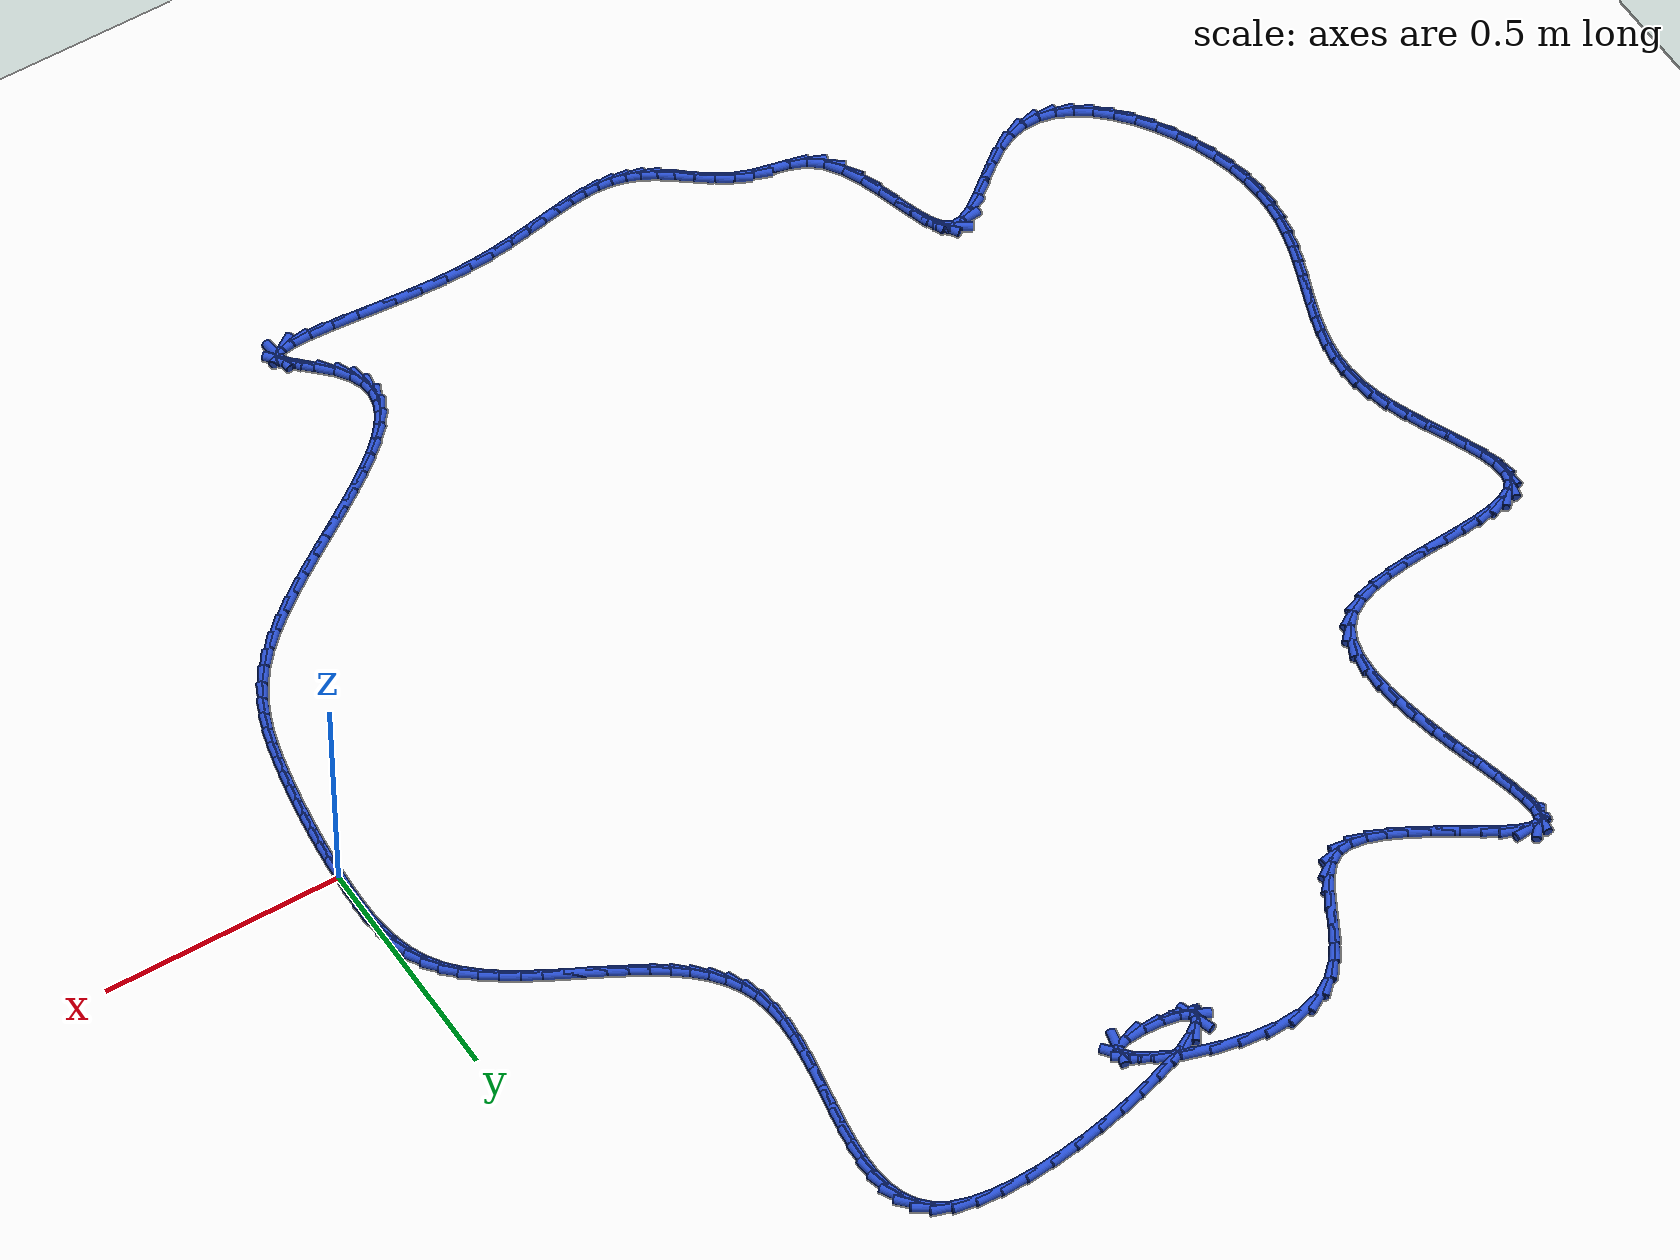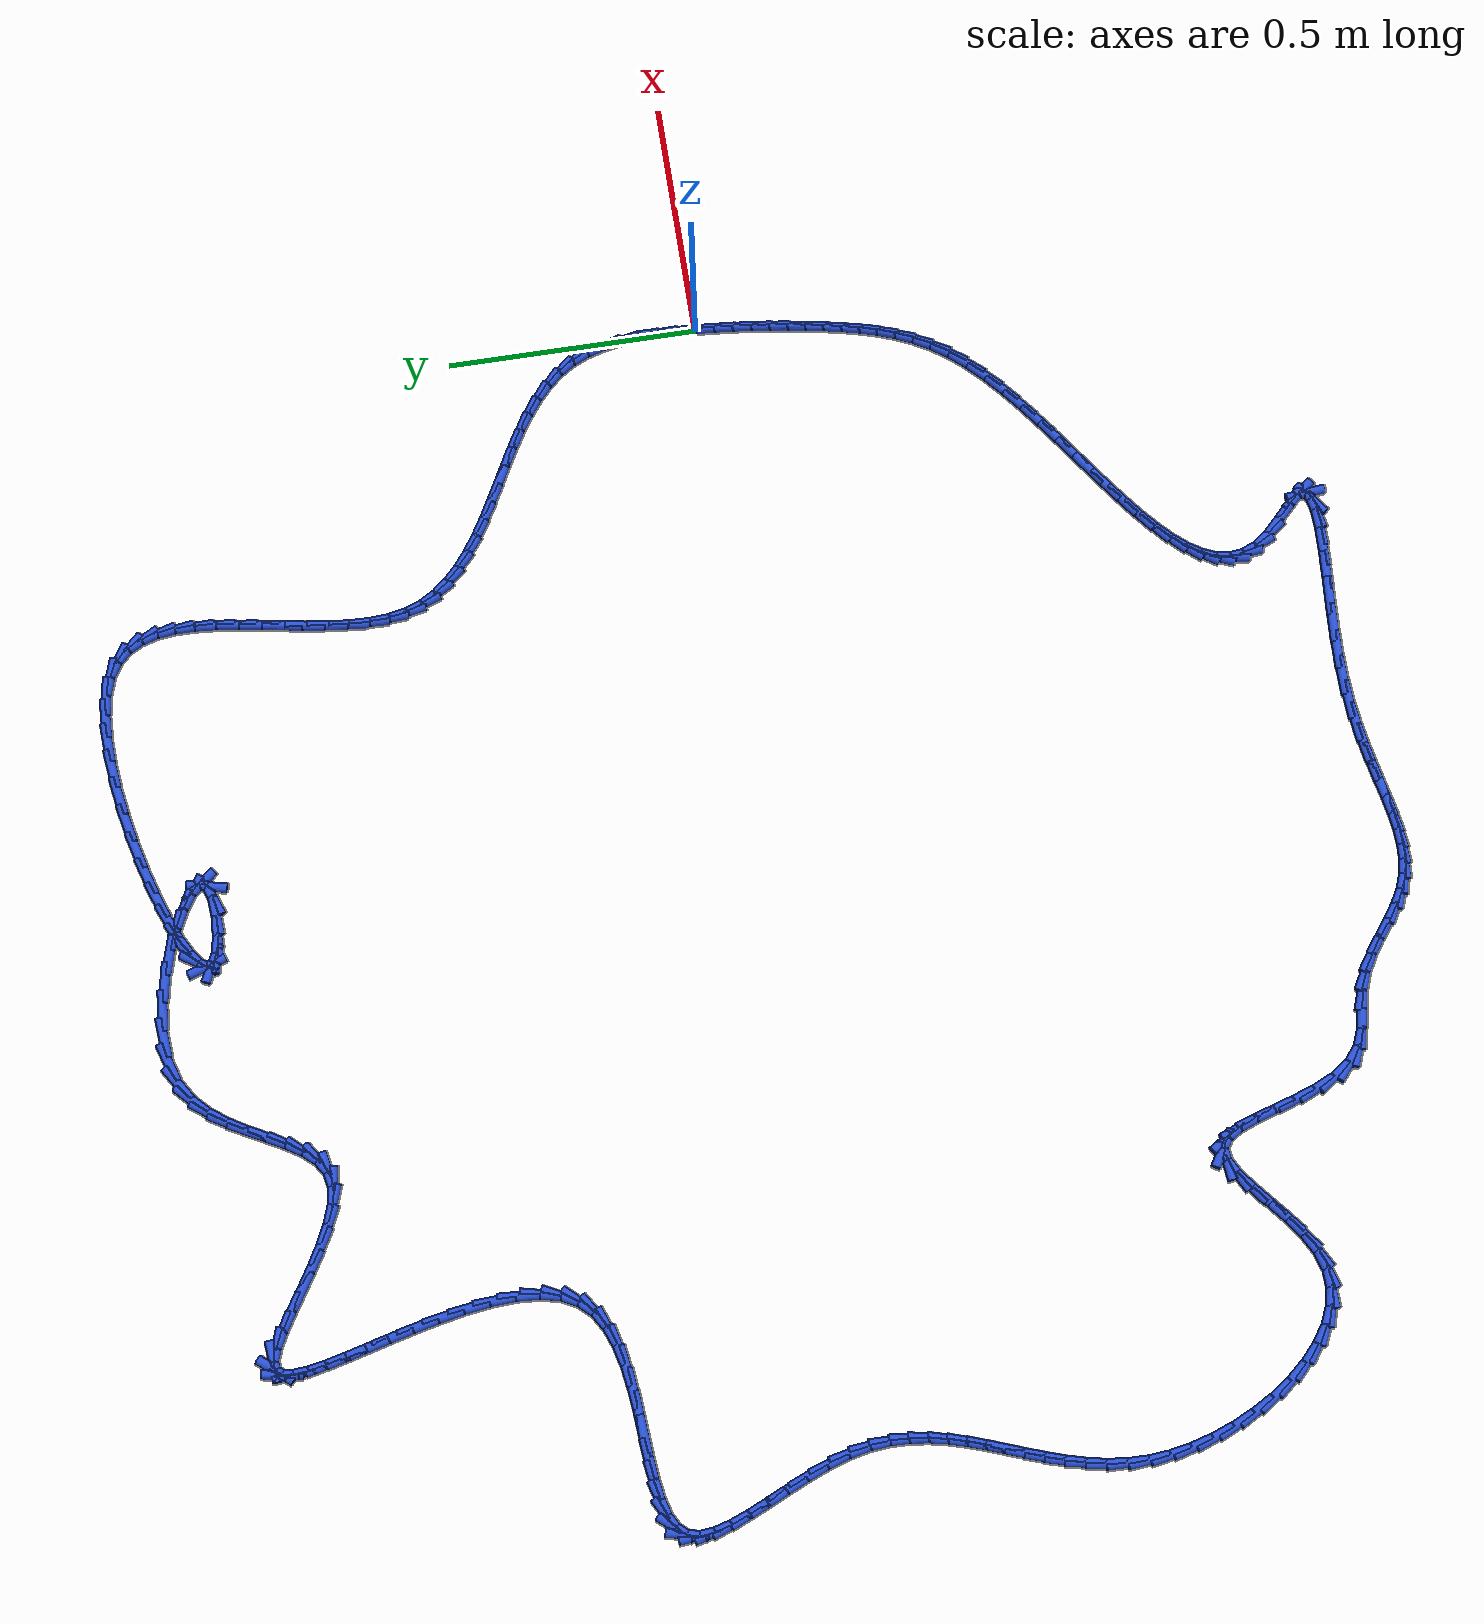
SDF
<sdf version="1.6">
 <world name="default">
  <light name="sun" type="directional">
   <pose>0 0 10 0 -0 0</pose>
   <diffuse>0.8 0.8 0.8 1</diffuse>
   <specular>0.2 0.2 0.2 1</specular>
   <attenuation>
    <range>1000</range>
    <constant>0.9</constant>
    <linear>0.01</linear>
    <quadratic>0.001</quadratic>
   </attenuation>
   <direction>-0.5 0.1 -0.9</direction>
  </light>
  <model name="ground_plane">
   <static>1</static>
   <link name="link">
    <collision name="collision">
     <geometry><plane><normal>0 0 1</normal><size>100 100</size></plane></geometry>
     <surface><friction><ode><mu>100</mu><mu2>50</mu2></ode></friction></surface>
    </collision>
    <visual name="visual">
     <cast_shadows>0</cast_shadows>
     <geometry><plane><normal>0 0 1</normal><size>100 100</size></plane></geometry>
     <material>
      <script><uri>file://media/materials/scripts/gazebo.material</uri><name>Gazebo/WhiteGlow</name></script>
     </material>
    </visual>
   </link>
  </model>
  <gravity>0 0 -9.8</gravity>
  <magnetic_field>6e-06 2.3e-05 -4.2e-05</magnetic_field>
  <atmosphere type="adiabatic"/>
  <physics name="default_physics" default="0" type="ode">
   <max_step_size>0.001</max_step_size>
   <real_time_factor>1</real_time_factor>
   <real_time_update_rate>1000</real_time_update_rate>
  </physics>
  <scene><ambient>0.4 0.4 0.4 1</ambient><background>0.7 0.7 0.7 1</background><shadows>1</shadows></scene>
  <spherical_coordinates>
   <surface_model>EARTH_WGS84</surface_model>
   <latitude_deg>0</latitude_deg>
   <longitude_deg>0</longitude_deg>
   <elevation>0</elevation>
   <heading_deg>0</heading_deg>
  </spherical_coordinates>
  <model name="line">
   <link name="link_0">
    <pose>-1.5178830414797062e-18 -2.7755575615628914e-17 0.01 0 1.57 1.5170530943298772</pose>
    <collision name="collision">
     <geometry><cylinder><radius>0.01</radius><length>0.08</length></cylinder></geometry>
    </collision>
    <visual name="visual">
     <material>
      <script><name>Gazebo/Blue</name><uri>file://media/materials/scripts/gazebo.material</uri></script>
     </material>
     <geometry><cylinder><radius>0.01</radius><length>0.08</length></cylinder></geometry>
    </visual>
   </link>
   <link name="link_1">
    <pose>0.0020785992189331615 0.03863923898723506 0.01 0 1.57 1.5495222511187354</pose>
    <collision name="collision">
     <geometry><cylinder><radius>0.01</radius><length>0.08</length></cylinder></geometry>
    </collision>
    <visual name="visual">
     <material>
      <script><name>Gazebo/Blue</name><uri>file://media/materials/scripts/gazebo.material</uri></script>
     </material>
     <geometry><cylinder><radius>0.01</radius><length>0.08</length></cylinder></geometry>
    </visual>
   </link>
   <link name="link_2">
    <pose>0.002904720988601142 0.07746570308452606 0.01 0 1.57 -1.5441596162405162</pose>
    <collision name="collision">
     <geometry><cylinder><radius>0.01</radius><length>0.08</length></cylinder></geometry>
    </collision>
    <visual name="visual">
     <material>
      <script><name>Gazebo/Blue</name><uri>file://media/materials/scripts/gazebo.material</uri></script>
     </material>
     <geometry><cylinder><radius>0.01</radius><length>0.08</length></cylinder></geometry>
    </visual>
   </link>
   <link name="link_3">
    <pose>0.0018789900140086437 0.11596476514933175 0.01 0 1.57 -1.4787251162206834</pose>
    <collision name="collision">
     <geometry><cylinder><radius>0.01</radius><length>0.08</length></cylinder></geometry>
    </collision>
    <visual name="visual">
     <material>
      <script><name>Gazebo/Blue</name><uri>file://media/materials/scripts/gazebo.material</uri></script>
     </material>
     <geometry><cylinder><radius>0.01</radius><length>0.08</length></cylinder></geometry>
    </visual>
   </link>
   <link name="link_4">
    <pose>-0.0015979689998396251 0.1536217980391109 0.01 0 1.57 -1.3928769809905095</pose>
    <collision name="collision">
     <geometry><cylinder><radius>0.01</radius><length>0.08</length></cylinder></geometry>
    </collision>
    <visual name="visual">
     <material>
      <script><name>Gazebo/Blue</name><uri>file://media/materials/scripts/gazebo.material</uri></script>
     </material>
     <geometry><cylinder><radius>0.01</radius><length>0.08</length></cylinder></geometry>
    </visual>
   </link>
   <link name="link_5">
    <pose>-0.00812553134793896 0.18992217461132221 0.01 0 1.57 -1.283373060486346</pose>
    <collision name="collision">
     <geometry><cylinder><radius>0.01</radius><length>0.08</length></cylinder></geometry>
    </collision>
    <visual name="visual">
     <material>
      <script><name>Gazebo/Blue</name><uri>file://media/materials/scripts/gazebo.material</uri></script>
     </material>
     <geometry><cylinder><radius>0.01</radius><length>0.08</length></cylinder></geometry>
    </visual>
   </link>
   <link name="link_6">
    <pose>-0.018303072325284664 0.22435126772342456 0.01 0 1.57 -1.1477487399118411</pose>
    <collision name="collision">
     <geometry><cylinder><radius>0.01</radius><length>0.08</length></cylinder></geometry>
    </collision>
    <visual name="visual">
     <material>
      <script><name>Gazebo/Blue</name><uri>file://media/materials/scripts/gazebo.material</uri></script>
     </material>
     <geometry><cylinder><radius>0.01</radius><length>0.08</length></cylinder></geometry>
    </visual>
   </link>
   <link name="link_7">
    <pose>-0.032729967226872006 0.25639445023287655 0.01 0 1.57 -0.9920843205776065</pose>
    <collision name="collision">
     <geometry><cylinder><radius>0.01</radius><length>0.08</length></cylinder></geometry>
    </collision>
    <visual name="visual">
     <material>
      <script><name>Gazebo/Blue</name><uri>file://media/materials/scripts/gazebo.material</uri></script>
     </material>
     <geometry><cylinder><radius>0.01</radius><length>0.08</length></cylinder></geometry>
    </visual>
   </link>
   <link name="link_8">
    <pose>-0.05184516821218978 0.28565259870171955 0.01 0 1.57 -0.8498550706622849</pose>
    <collision name="collision">
     <geometry><cylinder><radius>0.01</radius><length>0.08</length></cylinder></geometry>
    </collision>
    <visual name="visual">
     <material>
      <script><name>Gazebo/Blue</name><uri>file://media/materials/scripts/gazebo.material</uri></script>
     </material>
     <geometry><cylinder><radius>0.01</radius><length>0.08</length></cylinder></geometry>
    </visual>
   </link>
   <link name="link_9">
    <pose>-0.07527280861990056 0.312313254402616 0.01 0 1.57 -0.7336496715813939</pose>
    <collision name="collision">
     <geometry><cylinder><radius>0.01</radius><length>0.08</length></cylinder></geometry>
    </collision>
    <visual name="visual">
     <material>
      <script><name>Gazebo/Blue</name><uri>file://media/materials/scripts/gazebo.material</uri></script>
     </material>
     <geometry><cylinder><radius>0.01</radius><length>0.08</length></cylinder></geometry>
    </visual>
   </link>
   <link name="link_10">
    <pose>-0.10237895651911431 0.3367497640692885 0.01 0 1.57 -0.6429238868509911</pose>
    <collision name="collision">
     <geometry><cylinder><radius>0.01</radius><length>0.08</length></cylinder></geometry>
    </collision>
    <visual name="visual">
     <material>
      <script><name>Gazebo/Blue</name><uri>file://media/materials/scripts/gazebo.material</uri></script>
     </material>
     <geometry><cylinder><radius>0.01</radius><length>0.08</length></cylinder></geometry>
    </visual>
   </link>
   <link name="link_11">
    <pose>-0.1325295773471854 0.35933554832971304 0.01 0 1.57 -0.5751607206195366</pose>
    <collision name="collision">
     <geometry><cylinder><radius>0.01</radius><length>0.08</length></cylinder></geometry>
    </collision>
    <visual name="visual">
     <material>
      <script><name>Gazebo/Blue</name><uri>file://media/materials/scripts/gazebo.material</uri></script>
     </material>
     <geometry><cylinder><radius>0.01</radius><length>0.08</length></cylinder></geometry>
    </visual>
   </link>
   <link name="link_12">
    <pose>-0.16509063654146838 0.38044402781186626 0.01 0 1.57 -0.527518195686932</pose>
    <collision name="collision">
     <geometry><cylinder><radius>0.01</radius><length>0.08</length></cylinder></geometry>
    </collision>
    <visual name="visual">
     <material>
      <script><name>Gazebo/Blue</name><uri>file://media/materials/scripts/gazebo.material</uri></script>
     </material>
     <geometry><cylinder><radius>0.01</radius><length>0.08</length></cylinder></geometry>
    </visual>
   </link>
   <link name="link_13">
    <pose>-0.19942809953931767 0.40044862314372454 0.01 0 1.57 -0.4976398556508698</pose>
    <collision name="collision">
     <geometry><cylinder><radius>0.01</radius><length>0.08</length></cylinder></geometry>
    </collision>
    <visual name="visual">
     <material>
      <script><name>Gazebo/Blue</name><uri>file://media/materials/scripts/gazebo.material</uri></script>
     </material>
     <geometry><cylinder><radius>0.01</radius><length>0.08</length></cylinder></geometry>
    </visual>
   </link>
   <link name="link_14">
    <pose>-0.2349079317780876 0.4197227549532642 0.01 0 1.57 -0.4839544376546903</pose>
    <collision name="collision">
     <geometry><cylinder><radius>0.01</radius><length>0.08</length></cylinder></geometry>
    </collision>
    <visual name="visual">
     <material>
      <script><name>Gazebo/Blue</name><uri>file://media/materials/scripts/gazebo.material</uri></script>
     </material>
     <geometry><cylinder><radius>0.01</radius><length>0.08</length></cylinder></geometry>
    </visual>
   </link>
   <link name="link_15">
    <pose>-0.27089609869513287 0.4386398438684619 0.01 0 1.57 -0.4857541067202754</pose>
    <collision name="collision">
     <geometry><cylinder><radius>0.01</radius><length>0.08</length></cylinder></geometry>
    </collision>
    <visual name="visual">
     <material>
      <script><name>Gazebo/Blue</name><uri>file://media/materials/scripts/gazebo.material</uri></script>
     </material>
     <geometry><cylinder><radius>0.01</radius><length>0.08</length></cylinder></geometry>
    </visual>
   </link>
   <link name="link_16">
    <pose>-0.3067585657278078 0.4575733105172938 0.01 0 1.57 -0.50320975135911</pose>
    <collision name="collision">
     <geometry><cylinder><radius>0.01</radius><length>0.08</length></cylinder></geometry>
    </collision>
    <visual name="visual">
     <material>
      <script><name>Gazebo/Blue</name><uri>file://media/materials/scripts/gazebo.material</uri></script>
     </material>
     <geometry><cylinder><radius>0.01</radius><length>0.08</length></cylinder></geometry>
    </visual>
   </link>
   <link name="link_17">
    <pose>-0.3418612983134668 0.4768965755277364 0.01 0 1.57 -0.5373842920744916</pose>
    <collision name="collision">
     <geometry><cylinder><radius>0.01</radius><length>0.08</length></cylinder></geometry>
    </collision>
    <visual name="visual">
     <material>
      <script><name>Gazebo/Blue</name><uri>file://media/materials/scripts/gazebo.material</uri></script>
     </material>
     <geometry><cylinder><radius>0.01</radius><length>0.08</length></cylinder></geometry>
    </visual>
   </link>
   <link name="link_18">
    <pose>-0.37557026188946435 0.4969830595277662 0.01 0 1.57 -0.5902358637414826</pose>
    <collision name="collision">
     <geometry><cylinder><radius>0.01</radius><length>0.08</length></cylinder></geometry>
    </collision>
    <visual name="visual">
     <material>
      <script><name>Gazebo/Blue</name><uri>file://media/materials/scripts/gazebo.material</uri></script>
     </material>
     <geometry><cylinder><radius>0.01</radius><length>0.08</length></cylinder></geometry>
    </visual>
   </link>
   <link name="link_19">
    <pose>-0.407251421893155 0.5182061831453595 0.01 0 1.57 -0.6645249062836834</pose>
    <collision name="collision">
     <geometry><cylinder><radius>0.01</radius><length>0.08</length></cylinder></geometry>
    </collision>
    <visual name="visual">
     <material>
      <script><name>Gazebo/Blue</name><uri>file://media/materials/scripts/gazebo.material</uri></script>
     </material>
     <geometry><cylinder><radius>0.01</radius><length>0.08</length></cylinder></geometry>
    </visual>
   </link>
   <link name="link_20">
    <pose>-0.4362707437618932 0.5409393670084928 0.01 0 1.57 -0.7634155720979461</pose>
    <collision name="collision">
     <geometry><cylinder><radius>0.01</radius><length>0.08</length></cylinder></geometry>
    </collision>
    <visual name="visual">
     <material>
      <script><name>Gazebo/Blue</name><uri>file://media/materials/scripts/gazebo.material</uri></script>
     </material>
     <geometry><cylinder><radius>0.01</radius><length>0.08</length></cylinder></geometry>
    </visual>
   </link>
   <link name="link_21">
    <pose>-0.46199419293303334 0.5655560317451427 0.01 0 1.57 -0.8894046236103116</pose>
    <collision name="collision">
     <geometry><cylinder><radius>0.01</radius><length>0.08</length></cylinder></geometry>
    </collision>
    <visual name="visual">
     <material>
      <script><name>Gazebo/Blue</name><uri>file://media/materials/scripts/gazebo.material</uri></script>
     </material>
     <geometry><cylinder><radius>0.01</radius><length>0.08</length></cylinder></geometry>
    </visual>
   </link>
   <link name="link_22">
    <pose>-0.4837877348439299 0.5924295979832852 0.01 0 1.57 -1.04224156527305</pose>
    <collision name="collision">
     <geometry><cylinder><radius>0.01</radius><length>0.08</length></cylinder></geometry>
    </collision>
    <visual name="visual">
     <material>
      <script><name>Gazebo/Blue</name><uri>file://media/materials/scripts/gazebo.material</uri></script>
     </material>
     <geometry><cylinder><radius>0.01</radius><length>0.08</length></cylinder></geometry>
    </visual>
   </link>
   <link name="link_23">
    <pose>-0.5010173349319375 0.6219334863508972 0.01 0 1.57 -1.2159805231736438</pose>
    <collision name="collision">
     <geometry><cylinder><radius>0.01</radius><length>0.08</length></cylinder></geometry>
    </collision>
    <visual name="visual">
     <material>
      <script><name>Gazebo/Blue</name><uri>file://media/materials/scripts/gazebo.material</uri></script>
     </material>
     <geometry><cylinder><radius>0.01</radius><length>0.08</length></cylinder></geometry>
    </visual>
   </link>
   <link name="link_24">
    <pose>-0.5130592799717988 0.6544357450432797 0.01 0 1.57 -1.382666427620539</pose>
    <collision name="collision">
     <geometry><cylinder><radius>0.01</radius><length>0.08</length></cylinder></geometry>
    </collision>
    <visual name="visual">
     <material>
      <script><name>Gazebo/Blue</name><uri>file://media/materials/scripts/gazebo.material</uri></script>
     </material>
     <geometry><cylinder><radius>0.01</radius><length>0.08</length></cylinder></geometry>
    </visual>
   </link>
   <link name="link_25">
    <pose>-0.5198340738945745 0.6900211479161033 0.01 0 1.57 -1.5126613295837372</pose>
    <collision name="collision">
     <geometry><cylinder><radius>0.01</radius><length>0.08</length></cylinder></geometry>
    </collision>
    <visual name="visual">
     <material>
      <script><name>Gazebo/Blue</name><uri>file://media/materials/scripts/gazebo.material</uri></script>
     </material>
     <geometry><cylinder><radius>0.01</radius><length>0.08</length></cylinder></geometry>
    </visual>
   </link>
   <link name="link_26">
    <pose>-0.5220652134044766 0.7283564973500439 0.01 0 1.57 1.5336771816916435</pose>
    <collision name="collision">
     <geometry><cylinder><radius>0.01</radius><length>0.08</length></cylinder></geometry>
    </collision>
    <visual name="visual">
     <material>
      <script><name>Gazebo/Blue</name><uri>file://media/materials/scripts/gazebo.material</uri></script>
     </material>
     <geometry><cylinder><radius>0.01</radius><length>0.08</length></cylinder></geometry>
    </visual>
   </link>
   <link name="link_27">
    <pose>-0.5205543576118971 0.7690406732207347 0.01 0 1.57 1.467801363794704</pose>
    <collision name="collision">
     <geometry><cylinder><radius>0.01</radius><length>0.08</length></cylinder></geometry>
    </collision>
    <visual name="visual">
     <material>
      <script><name>Gazebo/Blue</name><uri>file://media/materials/scripts/gazebo.material</uri></script>
     </material>
     <geometry><cylinder><radius>0.01</radius><length>0.08</length></cylinder></geometry>
    </visual>
   </link>
   <link name="link_28">
    <pose>-0.5161636557785304 0.8115200843354847 0.01 0 1.57 1.4254953011933171</pose>
    <collision name="collision">
     <geometry><cylinder><radius>0.01</radius><length>0.08</length></cylinder></geometry>
    </collision>
    <visual name="visual">
     <material>
      <script><name>Gazebo/Blue</name><uri>file://media/materials/scripts/gazebo.material</uri></script>
     </material>
     <geometry><cylinder><radius>0.01</radius><length>0.08</length></cylinder></geometry>
    </visual>
   </link>
   <link name="link_29">
    <pose>-0.5097720464668061 0.8551988205031507 0.01 0 1.57 1.4027219726804094</pose>
    <collision name="collision">
     <geometry><cylinder><radius>0.01</radius><length>0.08</length></cylinder></geometry>
    </collision>
    <visual name="visual">
     <material>
      <script><name>Gazebo/Blue</name><uri>file://media/materials/scripts/gazebo.material</uri></script>
     </material>
     <geometry><cylinder><radius>0.01</radius><length>0.08</length></cylinder></geometry>
    </visual>
   </link>
   <link name="link_30">
    <pose>-0.502258468883107 0.8994809699094438 0.01 0 1.57 1.397421018821556</pose>
    <collision name="collision">
     <geometry><cylinder><radius>0.01</radius><length>0.08</length></cylinder></geometry>
    </collision>
    <visual name="visual">
     <material>
      <script><name>Gazebo/Blue</name><uri>file://media/materials/scripts/gazebo.material</uri></script>
     </material>
     <geometry><cylinder><radius>0.01</radius><length>0.08</length></cylinder></geometry>
    </visual>
   </link>
   <link name="link_31">
    <pose>-0.49450186223381654 0.9437706207400752 0.01 0 1.57 1.4092754066079751</pose>
    <collision name="collision">
     <geometry><cylinder><radius>0.01</radius><length>0.08</length></cylinder></geometry>
    </collision>
    <visual name="visual">
     <material>
      <script><name>Gazebo/Blue</name><uri>file://media/materials/scripts/gazebo.material</uri></script>
     </material>
     <geometry><cylinder><radius>0.01</radius><length>0.08</length></cylinder></geometry>
    </visual>
   </link>
   <link name="link_32">
    <pose>-0.48738116572531714 0.9874718611807559 0.01 0 1.57 1.4397026970054208</pose>
    <collision name="collision">
     <geometry><cylinder><radius>0.01</radius><length>0.08</length></cylinder></geometry>
    </collision>
    <visual name="visual">
     <material>
      <script><name>Gazebo/Blue</name><uri>file://media/materials/scripts/gazebo.material</uri></script>
     </material>
     <geometry><cylinder><radius>0.01</radius><length>0.08</length></cylinder></geometry>
    </visual>
   </link>
   <link name="link_33">
    <pose>-0.4817753185639928 1.0299887794171974 0.01 0 1.57 1.4921098379531508</pose>
    <collision name="collision">
     <geometry><cylinder><radius>0.01</radius><length>0.08</length></cylinder></geometry>
    </collision>
    <visual name="visual">
     <material>
      <script><name>Gazebo/Blue</name><uri>file://media/materials/scripts/gazebo.material</uri></script>
     </material>
     <geometry><cylinder><radius>0.01</radius><length>0.08</length></cylinder></geometry>
    </visual>
   </link>
   <link name="link_34">
    <pose>-0.47856325995622595 1.07072546363511 0.01 0 1.57 -1.56921477700065</pose>
    <collision name="collision">
     <geometry><cylinder><radius>0.01</radius><length>0.08</length></cylinder></geometry>
    </collision>
    <visual name="visual">
     <material>
      <script><name>Gazebo/Blue</name><uri>file://media/materials/scripts/gazebo.material</uri></script>
     </material>
     <geometry><cylinder><radius>0.01</radius><length>0.08</length></cylinder></geometry>
    </visual>
   </link>
   <link name="link_35">
    <pose>-0.4786239291084 1.1090860020202058 0.01 0 1.57 -1.4523224795311227</pose>
    <collision name="collision">
     <geometry><cylinder><radius>0.01</radius><length>0.08</length></cylinder></geometry>
    </collision>
    <visual name="visual">
     <material>
      <script><name>Gazebo/Blue</name><uri>file://media/materials/scripts/gazebo.material</uri></script>
     </material>
     <geometry><cylinder><radius>0.01</radius><length>0.08</length></cylinder></geometry>
    </visual>
   </link>
   <link name="link_36">
    <pose>-0.4828362652268979 1.144474482758195 0.01 0 1.57 -1.2881043076869754</pose>
    <collision name="collision">
     <geometry><cylinder><radius>0.01</radius><length>0.08</length></cylinder></geometry>
    </collision>
    <visual name="visual">
     <material>
      <script><name>Gazebo/Blue</name><uri>file://media/materials/scripts/gazebo.material</uri></script>
     </material>
     <geometry><cylinder><radius>0.01</radius><length>0.08</length></cylinder></geometry>
    </visual>
   </link>
   <link name="link_37">
    <pose>-0.49207920751810297 1.1762949940347898 0.01 0 1.57 -1.0695829565518729</pose>
    <collision name="collision">
     <geometry><cylinder><radius>0.01</radius><length>0.08</length></cylinder></geometry>
    </collision>
    <visual name="visual">
     <material>
      <script><name>Gazebo/Blue</name><uri>file://media/materials/scripts/gazebo.material</uri></script>
     </material>
     <geometry><cylinder><radius>0.01</radius><length>0.08</length></cylinder></geometry>
    </visual>
   </link>
   <link name="link_38">
    <pose>-0.5072316951883978 1.2039516240357002 0.01 0 1.57 -0.806713207750888</pose>
    <collision name="collision">
     <geometry><cylinder><radius>0.01</radius><length>0.08</length></cylinder></geometry>
    </collision>
    <visual name="visual">
     <material>
      <script><name>Gazebo/Blue</name><uri>file://media/materials/scripts/gazebo.material</uri></script>
     </material>
     <geometry><cylinder><radius>0.01</radius><length>0.08</length></cylinder></geometry>
    </visual>
   </link>
   <link name="link_39">
    <pose>-0.529172667444166 1.2268484609466377 0.01 0 1.57 -0.5348404785426674</pose>
    <collision name="collision">
     <geometry><cylinder><radius>0.01</radius><length>0.08</length></cylinder></geometry>
    </collision>
    <visual name="visual">
     <material>
      <script><name>Gazebo/Blue</name><uri>file://media/materials/scripts/gazebo.material</uri></script>
     </material>
     <geometry><cylinder><radius>0.01</radius><length>0.08</length></cylinder></geometry>
    </visual>
   </link>
   <link name="link_40">
    <pose>-0.5587810634917902 1.2443895929533135 0.01 0 1.57 -0.30150012228880224</pose>
    <collision name="collision">
     <geometry><cylinder><radius>0.01</radius><length>0.08</length></cylinder></geometry>
    </collision>
    <visual name="visual">
     <material>
      <script><name>Gazebo/Blue</name><uri>file://media/materials/scripts/gazebo.material</uri></script>
     </material>
     <geometry><cylinder><radius>0.01</radius><length>0.08</length></cylinder></geometry>
    </visual>
   </link>
   <link name="link_41">
    <pose>-0.5965880256604938 1.2561468278061299 0.01 0 1.57 -0.13986153490301337</pose>
    <collision name="collision">
     <geometry><cylinder><radius>0.01</radius><length>0.08</length></cylinder></geometry>
    </collision>
    <visual name="visual">
     <material>
      <script><name>Gazebo/Blue</name><uri>file://media/materials/scripts/gazebo.material</uri></script>
     </material>
     <geometry><cylinder><radius>0.01</radius><length>0.08</length></cylinder></geometry>
    </visual>
   </link>
   <link name="link_42">
    <pose>-0.6415094559805679 1.2624708974425594 0.01 0 1.57 -0.029062698073546524</pose>
    <collision name="collision">
     <geometry><cylinder><radius>0.01</radius><length>0.08</length></cylinder></geometry>
    </collision>
    <visual name="visual">
     <material>
      <script><name>Gazebo/Blue</name><uri>file://media/materials/scripts/gazebo.material</uri></script>
     </material>
     <geometry><cylinder><radius>0.01</radius><length>0.08</length></cylinder></geometry>
    </visual>
   </link>
   <link name="link_43">
    <pose>-0.6919926957781308 1.2639384898177854 0.01 0 1.57 0.05156101494900415</pose>
    <collision name="collision">
     <geometry><cylinder><radius>0.01</radius><length>0.08</length></cylinder></geometry>
    </collision>
    <visual name="visual">
     <material>
      <script><name>Gazebo/Blue</name><uri>file://media/materials/scripts/gazebo.material</uri></script>
     </material>
     <geometry><cylinder><radius>0.01</radius><length>0.08</length></cylinder></geometry>
    </visual>
   </link>
   <link name="link_44">
    <pose>-0.7464850366134486 1.2611263168857896 0.01 0 1.57 0.1139098649103487</pose>
    <collision name="collision">
     <geometry><cylinder><radius>0.01</radius><length>0.08</length></cylinder></geometry>
    </collision>
    <visual name="visual">
     <material>
      <script><name>Gazebo/Blue</name><uri>file://media/materials/scripts/gazebo.material</uri></script>
     </material>
     <geometry><cylinder><radius>0.01</radius><length>0.08</length></cylinder></geometry>
    </visual>
   </link>
   <link name="link_45">
    <pose>-0.8034337700467888 1.254611090600553 0.01 0 1.57 0.16514023611571838</pose>
    <collision name="collision">
     <geometry><cylinder><radius>0.01</radius><length>0.08</length></cylinder></geometry>
    </collision>
    <visual name="visual">
     <material>
      <script><name>Gazebo/Blue</name><uri>file://media/materials/scripts/gazebo.material</uri></script>
     </material>
     <geometry><cylinder><radius>0.01</radius><length>0.08</length></cylinder></geometry>
    </visual>
   </link>
   <link name="link_46">
    <pose>-0.861286187638417 1.244969522916057 0.01 0 1.57 0.20997869719354578</pose>
    <collision name="collision">
     <geometry><cylinder><radius>0.01</radius><length>0.08</length></cylinder></geometry>
    </collision>
    <visual name="visual">
     <material>
      <script><name>Gazebo/Blue</name><uri>file://media/materials/scripts/gazebo.material</uri></script>
     </material>
     <geometry><cylinder><radius>0.01</radius><length>0.08</length></cylinder></geometry>
    </visual>
   </link>
   <link name="link_47">
    <pose>-0.9184895809486004 1.2327783257862825 0.01 0 1.57 0.2520451746422954</pose>
    <collision name="collision">
     <geometry><cylinder><radius>0.01</radius><length>0.08</length></cylinder></geometry>
    </collision>
    <visual name="visual">
     <material>
      <script><name>Gazebo/Blue</name><uri>file://media/materials/scripts/gazebo.material</uri></script>
     </material>
     <geometry><cylinder><radius>0.01</radius><length>0.08</length></cylinder></geometry>
    </visual>
   </link>
   <link name="link_48">
    <pose>-0.9734912415376056 1.218614211165211 0.01 0 1.57 0.2947860011651701</pose>
    <collision name="collision">
     <geometry><cylinder><radius>0.01</radius><length>0.08</length></cylinder></geometry>
    </collision>
    <visual name="visual">
     <material>
      <script><name>Gazebo/Blue</name><uri>file://media/materials/scripts/gazebo.material</uri></script>
     </material>
     <geometry><cylinder><radius>0.01</radius><length>0.08</length></cylinder></geometry>
    </visual>
   </link>
   <link name="link_49">
    <pose>-1.0247384609656986 1.203053891006824 0.01 0 1.57 0.34249576800314135</pose>
    <collision name="collision">
     <geometry><cylinder><radius>0.01</radius><length>0.08</length></cylinder></geometry>
    </collision>
    <visual name="visual">
     <material>
      <script><name>Gazebo/Blue</name><uri>file://media/materials/scripts/gazebo.material</uri></script>
     </material>
     <geometry><cylinder><radius>0.01</radius><length>0.08</length></cylinder></geometry>
    </visual>
   </link>
   <link name="link_50">
    <pose>-1.0706785307931466 1.1866740772651025 0.01 0 1.57 0.4021633208694779</pose>
    <collision name="collision">
     <geometry><cylinder><radius>0.01</radius><length>0.08</length></cylinder></geometry>
    </collision>
    <visual name="visual">
     <material>
      <script><name>Gazebo/Blue</name><uri>file://media/materials/scripts/gazebo.material</uri></script>
     </material>
     <geometry><cylinder><radius>0.01</radius><length>0.08</length></cylinder></geometry>
    </visual>
   </link>
   <link name="link_51">
    <pose>-1.1097587425802156 1.1700514818940277 0.01 0 1.57 0.4882443927290785</pose>
    <collision name="collision">
     <geometry><cylinder><radius>0.01</radius><length>0.08</length></cylinder></geometry>
    </collision>
    <visual name="visual">
     <material>
      <script><name>Gazebo/Blue</name><uri>file://media/materials/scripts/gazebo.material</uri></script>
     </material>
     <geometry><cylinder><radius>0.01</radius><length>0.08</length></cylinder></geometry>
    </visual>
   </link>
   <link name="link_52">
    <pose>-1.1404263878871725 1.1537628168475809 0.01 0 1.57 0.6388865633801648</pose>
    <collision name="collision">
     <geometry><cylinder><radius>0.01</radius><length>0.08</length></cylinder></geometry>
    </collision>
    <visual name="visual">
     <material>
      <script><name>Gazebo/Blue</name><uri>file://media/materials/scripts/gazebo.material</uri></script>
     </material>
     <geometry><cylinder><radius>0.01</radius><length>0.08</length></cylinder></geometry>
    </visual>
   </link>
   <link name="link_53">
    <pose>-1.161128758274284 1.1383847940797436 0.01 0 1.57 0.9865940551335252</pose>
    <collision name="collision">
     <geometry><cylinder><radius>0.01</radius><length>0.08</length></cylinder></geometry>
    </collision>
    <visual name="visual">
     <material>
      <script><name>Gazebo/Blue</name><uri>file://media/materials/scripts/gazebo.material</uri></script>
     </material>
     <geometry><cylinder><radius>0.01</radius><length>0.08</length></cylinder></geometry>
    </visual>
   </link>
   <link name="link_54">
    <pose>-1.1703131453018165 1.1244941255444962 0.01 0 1.57 -1.253305451888202</pose>
    <collision name="collision">
     <geometry><cylinder><radius>0.01</radius><length>0.08</length></cylinder></geometry>
    </collision>
    <visual name="visual">
     <material>
      <script><name>Gazebo/Blue</name><uri>file://media/materials/scripts/gazebo.material</uri></script>
     </material>
     <geometry><cylinder><radius>0.01</radius><length>0.08</length></cylinder></geometry>
    </visual>
   </link>
   <link name="link_55">
    <pose>-1.166426840530037 1.1126675231958216 0.01 0 1.57 -0.4606597184284638</pose>
    <collision name="collision">
     <geometry><cylinder><radius>0.01</radius><length>0.08</length></cylinder></geometry>
    </collision>
    <visual name="visual">
     <material>
      <script><name>Gazebo/Blue</name><uri>file://media/materials/scripts/gazebo.material</uri></script>
     </material>
     <geometry><cylinder><radius>0.01</radius><length>0.08</length></cylinder></geometry>
    </visual>
   </link>
   <link name="link_56">
    <pose>-1.147917135519211 1.1034816989876992 0.01 0 1.57 -0.17444849027638426</pose>
    <collision name="collision">
     <geometry><cylinder><radius>0.01</radius><length>0.08</length></cylinder></geometry>
    </collision>
    <visual name="visual">
     <material>
      <script><name>Gazebo/Blue</name><uri>file://media/materials/scripts/gazebo.material</uri></script>
     </material>
     <geometry><cylinder><radius>0.01</radius><length>0.08</length></cylinder></geometry>
    </visual>
   </link>
   <link name="link_57">
    <pose>-1.1141341298390697 1.0975277847051539 0.01 0 1.57 -0.04801757474055738</pose>
    <collision name="collision">
     <geometry><cylinder><radius>0.01</radius><length>0.08</length></cylinder></geometry>
    </collision>
    <visual name="visual">
     <material>
      <script><name>Gazebo/Blue</name><uri>file://media/materials/scripts/gazebo.material</uri></script>
     </material>
     <geometry><cylinder><radius>0.01</radius><length>0.08</length></cylinder></geometry>
    </visual>
   </link>
   <link name="link_58">
    <pose>-1.0724614775467658 1.0955252256806818 0.01 0 1.57 0.07192654719083427</pose>
    <collision name="collision">
     <geometry><cylinder><radius>0.01</radius><length>0.08</length></cylinder></geometry>
    </collision>
    <visual name="visual">
     <material>
      <script><name>Gazebo/Blue</name><uri>file://media/materials/scripts/gazebo.material</uri></script>
     </material>
     <geometry><cylinder><radius>0.01</radius><length>0.08</length></cylinder></geometry>
    </visual>
   </link>
   <link name="link_59">
    <pose>-1.03449497103619 1.098260744367171 0.01 0 1.57 0.34499766526176945</pose>
    <collision name="collision">
     <geometry><cylinder><radius>0.01</radius><length>0.08</length></cylinder></geometry>
    </collision>
    <visual name="visual">
     <material>
      <script><name>Gazebo/Blue</name><uri>file://media/materials/scripts/gazebo.material</uri></script>
     </material>
     <geometry><cylinder><radius>0.01</radius><length>0.08</length></cylinder></geometry>
    </visual>
   </link>
   <link name="link_60">
    <pose>-1.011620955819144 1.1064809770505448 0.01 0 1.57 1.3429377472638806</pose>
    <collision name="collision">
     <geometry><cylinder><radius>0.01</radius><length>0.08</length></cylinder></geometry>
    </collision>
    <visual name="visual">
     <material>
      <script><name>Gazebo/Blue</name><uri>file://media/materials/scripts/gazebo.material</uri></script>
     </material>
     <geometry><cylinder><radius>0.01</radius><length>0.08</length></cylinder></geometry>
    </visual>
   </link>
   <link name="link_61">
    <pose>-1.0085261344128973 1.1198273015198252 0.01 0 1.57 -0.8775524399654754</pose>
    <collision name="collision">
     <geometry><cylinder><radius>0.01</radius><length>0.08</length></cylinder></geometry>
    </collision>
    <visual name="visual">
     <material>
      <script><name>Gazebo/Blue</name><uri>file://media/materials/scripts/gazebo.material</uri></script>
     </material>
     <geometry><cylinder><radius>0.01</radius><length>0.08</length></cylinder></geometry>
    </visual>
   </link>
   <link name="link_62">
    <pose>-1.0225710255122034 1.1367324749067405 0.01 0 1.57 -0.5893144285496988</pose>
    <collision name="collision">
     <geometry><cylinder><radius>0.01</radius><length>0.08</length></cylinder></geometry>
    </collision>
    <visual name="visual">
     <material>
      <script><name>Gazebo/Blue</name><uri>file://media/materials/scripts/gazebo.material</uri></script>
     </material>
     <geometry><cylinder><radius>0.01</radius><length>0.08</length></cylinder></geometry>
    </visual>
   </link>
   <link name="link_63">
    <pose>-1.0507439436930441 1.1555678508077571 0.01 0 1.57 -0.4532566293506664</pose>
    <collision name="collision">
     <geometry><cylinder><radius>0.01</radius><length>0.08</length></cylinder></geometry>
    </collision>
    <visual name="visual">
     <material>
      <script><name>Gazebo/Blue</name><uri>file://media/materials/scripts/gazebo.material</uri></script>
     </material>
     <geometry><cylinder><radius>0.01</radius><length>0.08</length></cylinder></geometry>
    </visual>
   </link>
   <link name="link_64">
    <pose>-1.0900332035314002 1.1747047828193413 0.01 0 1.57 -0.35945721357032306</pose>
    <collision name="collision">
     <geometry><cylinder><radius>0.01</radius><length>0.08</length></cylinder></geometry>
    </collision>
    <visual name="visual">
     <material>
      <script><name>Gazebo/Blue</name><uri>file://media/materials/scripts/gazebo.material</uri></script>
     </material>
     <geometry><cylinder><radius>0.01</radius><length>0.08</length></cylinder></geometry>
    </visual>
   </link>
   <link name="link_65">
    <pose>-1.137427119603253 1.1925146245379599 0.01 0 1.57 -0.27579400454257824</pose>
    <collision name="collision">
     <geometry><cylinder><radius>0.01</radius><length>0.08</length></cylinder></geometry>
    </collision>
    <visual name="visual">
     <material>
      <script><name>Gazebo/Blue</name><uri>file://media/materials/scripts/gazebo.material</uri></script>
     </material>
     <geometry><cylinder><radius>0.01</radius><length>0.08</length></cylinder></geometry>
    </visual>
   </link>
   <link name="link_66">
    <pose>-1.1899140064845848 1.2073687295600792 0.01 0 1.57 -0.18602394724387952</pose>
    <collision name="collision">
     <geometry><cylinder><radius>0.01</radius><length>0.08</length></cylinder></geometry>
    </collision>
    <visual name="visual">
     <material>
      <script><name>Gazebo/Blue</name><uri>file://media/materials/scripts/gazebo.material</uri></script>
     </material>
     <geometry><cylinder><radius>0.01</radius><length>0.08</length></cylinder></geometry>
    </visual>
   </link>
   <link name="link_67">
    <pose>-1.244482178751375 1.2176384514821652 0.01 0 1.57 -0.07548754934938565</pose>
    <collision name="collision">
     <geometry><cylinder><radius>0.01</radius><length>0.08</length></cylinder></geometry>
    </collision>
    <visual name="visual">
     <material>
      <script><name>Gazebo/Blue</name><uri>file://media/materials/scripts/gazebo.material</uri></script>
     </material>
     <geometry><cylinder><radius>0.01</radius><length>0.08</length></cylinder></geometry>
    </visual>
   </link>
   <link name="link_68">
    <pose>-1.2981199509796055 1.221695143900685 0.01 0 1.57 0.07601645962911668</pose>
    <collision name="collision">
     <geometry><cylinder><radius>0.01</radius><length>0.08</length></cylinder></geometry>
    </collision>
    <visual name="visual">
     <material>
      <script><name>Gazebo/Blue</name><uri>file://media/materials/scripts/gazebo.material</uri></script>
     </material>
     <geometry><cylinder><radius>0.01</radius><length>0.08</length></cylinder></geometry>
    </visual>
   </link>
   <link name="link_69">
    <pose>-1.347815637745258 1.217910160412104 0.01 0 1.57 0.29694587534450034</pose>
    <collision name="collision">
     <geometry><cylinder><radius>0.01</radius><length>0.08</length></cylinder></geometry>
    </collision>
    <visual name="visual">
     <material>
      <script><name>Gazebo/Blue</name><uri>file://media/materials/scripts/gazebo.material</uri></script>
     </material>
     <geometry><cylinder><radius>0.01</radius><length>0.08</length></cylinder></geometry>
    </visual>
   </link>
   <link name="link_70">
    <pose>-1.3907080932190066 1.2047853681177356 0.01 0 1.57 0.5531061286805906</pose>
    <collision name="collision">
     <geometry><cylinder><radius>0.01</radius><length>0.08</length></cylinder></geometry>
    </collision>
    <visual name="visual">
     <material>
      <script><name>Gazebo/Blue</name><uri>file://media/materials/scripts/gazebo.material</uri></script>
     </material>
     <geometry><cylinder><radius>0.01</radius><length>0.08</length></cylinder></geometry>
    </visual>
   </link>
   <link name="link_71">
    <pose>-1.4262591598740235 1.1828365982569913 0.01 0 1.57 0.771271952233313</pose>
    <collision name="collision">
     <geometry><cylinder><radius>0.01</radius><length>0.08</length></cylinder></geometry>
    </collision>
    <visual name="visual">
     <material>
      <script><name>Gazebo/Blue</name><uri>file://media/materials/scripts/gazebo.material</uri></script>
     </material>
     <geometry><cylinder><radius>0.01</radius><length>0.08</length></cylinder></geometry>
    </visual>
   </link>
   <link name="link_72">
    <pose>-1.4557556623883396 1.1541618892243086 0.01 0 1.57 0.9305191412809647</pose>
    <collision name="collision">
     <geometry><cylinder><radius>0.01</radius><length>0.08</length></cylinder></geometry>
    </collision>
    <visual name="visual">
     <material>
      <script><name>Gazebo/Blue</name><uri>file://media/materials/scripts/gazebo.material</uri></script>
     </material>
     <geometry><cylinder><radius>0.01</radius><length>0.08</length></cylinder></geometry>
    </visual>
   </link>
   <link name="link_73">
    <pose>-1.4805335425568877 1.120901862543751 0.01 0 1.57 1.030946109857092</pose>
    <collision name="collision">
     <geometry><cylinder><radius>0.01</radius><length>0.08</length></cylinder></geometry>
    </collision>
    <visual name="visual">
     <material>
      <script><name>Gazebo/Blue</name><uri>file://media/materials/scripts/gazebo.material</uri></script>
     </material>
     <geometry><cylinder><radius>0.01</radius><length>0.08</length></cylinder></geometry>
    </visual>
   </link>
   <link name="link_74">
    <pose>-1.5019287421746026 1.0851971397393836 0.01 0 1.57 1.0777357255396238</pose>
    <collision name="collision">
     <geometry><cylinder><radius>0.01</radius><length>0.08</length></cylinder></geometry>
    </collision>
    <visual name="visual">
     <material>
      <script><name>Gazebo/Blue</name><uri>file://media/materials/scripts/gazebo.material</uri></script>
     </material>
     <geometry><cylinder><radius>0.01</radius><length>0.08</length></cylinder></geometry>
    </visual>
   </link>
   <link name="link_75">
    <pose>-1.5212772030364152 1.049188342335271 0.01 0 1.57 1.071488971842338</pose>
    <collision name="collision">
     <geometry><cylinder><radius>0.01</radius><length>0.08</length></cylinder></geometry>
    </collision>
    <visual name="visual">
     <material>
      <script><name>Gazebo/Blue</name><uri>file://media/materials/scripts/gazebo.material</uri></script>
     </material>
     <geometry><cylinder><radius>0.01</radius><length>0.08</length></cylinder></geometry>
    </visual>
   </link>
   <link name="link_76">
    <pose>-1.5399148669372602 1.0150160918554785 0.01 0 1.57 1.0029421887544863</pose>
    <collision name="collision">
     <geometry><cylinder><radius>0.01</radius><length>0.08</length></cylinder></geometry>
    </collision>
    <visual name="visual">
     <material>
      <script><name>Gazebo/Blue</name><uri>file://media/materials/scripts/gazebo.material</uri></script>
     </material>
     <geometry><cylinder><radius>0.01</radius><length>0.08</length></cylinder></geometry>
    </visual>
   </link>
   <link name="link_77">
    <pose>-1.5591776756720708 0.9848210098240698 0.01 0 1.57 0.8483023012357603</pose>
    <collision name="collision">
     <geometry><cylinder><radius>0.01</radius><length>0.08</length></cylinder></geometry>
    </collision>
    <visual name="visual">
     <material>
      <script><name>Gazebo/Blue</name><uri>file://media/materials/scripts/gazebo.material</uri></script>
     </material>
     <geometry><cylinder><radius>0.01</radius><length>0.08</length></cylinder></geometry>
    </visual>
   </link>
   <link name="link_78">
    <pose>-1.5804015710357797 0.9607437177651093 0.01 0 1.57 0.572935323096822</pose>
    <collision name="collision">
     <geometry><cylinder><radius>0.01</radius><length>0.08</length></cylinder></geometry>
    </collision>
    <visual name="visual">
     <material>
      <script><name>Gazebo/Blue</name><uri>file://media/materials/scripts/gazebo.material</uri></script>
     </material>
     <geometry><cylinder><radius>0.01</radius><length>0.08</length></cylinder></geometry>
    </visual>
   </link>
   <link name="link_79">
    <pose>-1.6049224948233203 0.9449248372026622 0.01 0 1.57 0.1875647733040756</pose>
    <collision name="collision">
     <geometry><cylinder><radius>0.01</radius><length>0.08</length></cylinder></geometry>
    </collision>
    <visual name="visual">
     <material>
      <script><name>Gazebo/Blue</name><uri>file://media/materials/scripts/gazebo.material</uri></script>
     </material>
     <geometry><cylinder><radius>0.01</radius><length>0.08</length></cylinder></geometry>
    </visual>
   </link>
   <link name="link_80">
    <pose>-1.63401449266159 0.9394033006288797 0.01 0 1.57 -0.13828781224541964</pose>
    <collision name="collision">
     <geometry><cylinder><radius>0.01</radius><length>0.08</length></cylinder></geometry>
    </collision>
    <visual name="visual">
     <material>
      <script><name>Gazebo/Blue</name><uri>file://media/materials/scripts/gazebo.material</uri></script>
     </material>
     <geometry><cylinder><radius>0.01</radius><length>0.08</length></cylinder></geometry>
    </visual>
   </link>
   <link name="link_81">
    <pose>-1.6676532793122019 0.9440850165865383 0.01 0 1.57 -0.3328378080375104</pose>
    <collision name="collision">
     <geometry><cylinder><radius>0.01</radius><length>0.08</length></cylinder></geometry>
    </collision>
    <visual name="visual">
     <material>
      <script><name>Gazebo/Blue</name><uri>file://media/materials/scripts/gazebo.material</uri></script>
     </material>
     <geometry><cylinder><radius>0.01</radius><length>0.08</length></cylinder></geometry>
    </visual>
   </link>
   <link name="link_82">
    <pose>-1.7045822458619588 0.9568513126876004 0.01 0 1.57 -0.4469678608361376</pose>
    <collision name="collision">
     <geometry><cylinder><radius>0.01</radius><length>0.08</length></cylinder></geometry>
    </collision>
    <visual name="visual">
     <material>
      <script><name>Gazebo/Blue</name><uri>file://media/materials/scripts/gazebo.material</uri></script>
     </material>
     <geometry><cylinder><radius>0.01</radius><length>0.08</length></cylinder></geometry>
    </visual>
   </link>
   <link name="link_83">
    <pose>-1.7434960999356945 0.9755035346279384 0.01 0 1.57 -0.513696573319698</pose>
    <collision name="collision">
     <geometry><cylinder><radius>0.01</radius><length>0.08</length></cylinder></geometry>
    </collision>
    <visual name="visual">
     <material>
      <script><name>Gazebo/Blue</name><uri>file://media/materials/scripts/gazebo.material</uri></script>
     </material>
     <geometry><cylinder><radius>0.01</radius><length>0.08</length></cylinder></geometry>
    </visual>
   </link>
   <link name="link_84">
    <pose>-1.7830895491582406 0.9978430281034236 0.01 0 1.57 -0.5488199919390537</pose>
    <collision name="collision">
     <geometry><cylinder><radius>0.01</radius><length>0.08</length></cylinder></geometry>
    </collision>
    <visual name="visual">
     <material>
      <script><name>Gazebo/Blue</name><uri>file://media/materials/scripts/gazebo.material</uri></script>
     </material>
     <geometry><cylinder><radius>0.01</radius><length>0.08</length></cylinder></geometry>
    </visual>
   </link>
   <link name="link_85">
    <pose>-1.8220573011544303 1.0216711388099289 0.01 0 1.57 -0.5580185144194386</pose>
    <collision name="collision">
     <geometry><cylinder><radius>0.01</radius><length>0.08</length></cylinder></geometry>
    </collision>
    <visual name="visual">
     <material>
      <script><name>Gazebo/Blue</name><uri>file://media/materials/scripts/gazebo.material</uri></script>
     </material>
     <geometry><cylinder><radius>0.01</radius><length>0.08</length></cylinder></geometry>
    </visual>
   </link>
   <link name="link_86">
    <pose>-1.859094063549096 1.0447892124433258 0.01 0 1.57 -0.5388755868270649</pose>
    <collision name="collision">
     <geometry><cylinder><radius>0.01</radius><length>0.08</length></cylinder></geometry>
    </collision>
    <visual name="visual">
     <material>
      <script><name>Gazebo/Blue</name><uri>file://media/materials/scripts/gazebo.material</uri></script>
     </material>
     <geometry><cylinder><radius>0.01</radius><length>0.08</length></cylinder></geometry>
    </visual>
   </link>
   <link name="link_87">
    <pose>-1.892894543967069 1.0649985946994858 0.01 0 1.57 -0.4764853854381218</pose>
    <collision name="collision">
     <geometry><cylinder><radius>0.01</radius><length>0.08</length></cylinder></geometry>
    </collision>
    <visual name="visual">
     <material>
      <script><name>Gazebo/Blue</name><uri>file://media/materials/scripts/gazebo.material</uri></script>
     </material>
     <geometry><cylinder><radius>0.01</radius><length>0.08</length></cylinder></geometry>
    </visual>
   </link>
   <link name="link_88">
    <pose>-1.9221534500331827 1.0801006312742816 0.01 0 1.57 -0.3214438914504846</pose>
    <collision name="collision">
     <geometry><cylinder><radius>0.01</radius><length>0.08</length></cylinder></geometry>
    </collision>
    <visual name="visual">
     <material>
      <script><name>Gazebo/Blue</name><uri>file://media/materials/scripts/gazebo.material</uri></script>
     </material>
     <geometry><cylinder><radius>0.01</radius><length>0.08</length></cylinder></geometry>
    </visual>
   </link>
   <link name="link_89">
    <pose>-1.94556548937227 1.087896667863585 0.01 0 1.57 0.09702985640388945</pose>
    <collision name="collision">
     <geometry><cylinder><radius>0.01</radius><length>0.08</length></cylinder></geometry>
    </collision>
    <visual name="visual">
     <material>
      <script><name>Gazebo/Blue</name><uri>file://media/materials/scripts/gazebo.material</uri></script>
     </material>
     <geometry><cylinder><radius>0.01</radius><length>0.08</length></cylinder></geometry>
    </visual>
   </link>
   <link name="link_90">
    <pose>-1.9619079806813127 1.0863059630904266 0.01 0 1.57 0.8818022737360411</pose>
    <collision name="collision">
     <geometry><cylinder><radius>0.01</radius><length>0.08</length></cylinder></geometry>
    </collision>
    <visual name="visual">
     <material>
      <script><name>Gazebo/Blue</name><uri>file://media/materials/scripts/gazebo.material</uri></script>
     </material>
     <geometry><cylinder><radius>0.01</radius><length>0.08</length></cylinder></geometry>
    </visual>
   </link>
   <link name="link_91">
    <pose>-1.9712016015454716 1.075022453985907 0.01 0 1.57 1.410156198600101</pose>
    <collision name="collision">
     <geometry><cylinder><radius>0.01</radius><length>0.08</length></cylinder></geometry>
    </collision>
    <visual name="visual">
     <material>
      <script><name>Gazebo/Blue</name><uri>file://media/materials/scripts/gazebo.material</uri></script>
     </material>
     <geometry><cylinder><radius>0.01</radius><length>0.08</length></cylinder></geometry>
    </visual>
   </link>
   <link name="link_92">
    <pose>-1.9744278925620655 1.055111542294181 0.01 0 1.57 -1.5040318441585454</pose>
    <collision name="collision">
     <geometry><cylinder><radius>0.01</radius><length>0.08</length></cylinder></geometry>
    </collision>
    <visual name="visual">
     <material>
      <script><name>Gazebo/Blue</name><uri>file://media/materials/scripts/gazebo.material</uri></script>
     </material>
     <geometry><cylinder><radius>0.01</radius><length>0.08</length></cylinder></geometry>
    </visual>
   </link>
   <link name="link_93">
    <pose>-1.9725933270602438 1.0276742168945825 0.01 0 1.57 -1.3986119691807803</pose>
    <collision name="collision">
     <geometry><cylinder><radius>0.01</radius><length>0.08</length></cylinder></geometry>
    </collision>
    <visual name="visual">
     <material>
      <script><name>Gazebo/Blue</name><uri>file://media/materials/scripts/gazebo.material</uri></script>
     </material>
     <geometry><cylinder><radius>0.01</radius><length>0.08</length></cylinder></geometry>
    </visual>
   </link>
   <link name="link_94">
    <pose>-1.9667043783691551 0.9938114666664462 0.01 0 1.57 -1.346575399080289</pose>
    <collision name="collision">
     <geometry><cylinder><radius>0.01</radius><length>0.08</length></cylinder></geometry>
    </collision>
    <visual name="visual">
     <material>
      <script><name>Gazebo/Blue</name><uri>file://media/materials/scripts/gazebo.material</uri></script>
     </material>
     <geometry><cylinder><radius>0.01</radius><length>0.08</length></cylinder></geometry>
    </visual>
   </link>
   <link name="link_95">
    <pose>-1.9577675198179472 0.9546242804891049 0.01 0 1.57 -1.3230956206269366</pose>
    <collision name="collision">
     <geometry><cylinder><radius>0.01</radius><length>0.08</length></cylinder></geometry>
    </collision>
    <visual name="visual">
     <material>
      <script><name>Gazebo/Blue</name><uri>file://media/materials/scripts/gazebo.material</uri></script>
     </material>
     <geometry><cylinder><radius>0.01</radius><length>0.08</length></cylinder></geometry>
    </visual>
   </link>
   <link name="link_96">
    <pose>-1.946789224735768 0.9112136472418919 0.01 0 1.57 -1.3181469825982528</pose>
    <collision name="collision">
     <geometry><cylinder><radius>0.01</radius><length>0.08</length></cylinder></geometry>
    </collision>
    <visual name="visual">
     <material>
      <script><name>Gazebo/Blue</name><uri>file://media/materials/scripts/gazebo.material</uri></script>
     </material>
     <geometry><cylinder><radius>0.01</radius><length>0.08</length></cylinder></geometry>
    </visual>
   </link>
   <link name="link_97">
    <pose>-1.934775966451767 0.8646805558041422 0.01 0 1.57 -1.327696688601335</pose>
    <collision name="collision">
     <geometry><cylinder><radius>0.01</radius><length>0.08</length></cylinder></geometry>
    </collision>
    <visual name="visual">
     <material>
      <script><name>Gazebo/Blue</name><uri>file://media/materials/scripts/gazebo.material</uri></script>
     </material>
     <geometry><cylinder><radius>0.01</radius><length>0.08</length></cylinder></geometry>
    </visual>
   </link>
   <link name="link_98">
    <pose>-1.9227342182950915 0.8161259950551885 0.01 0 1.57 -1.350792773091679</pose>
    <collision name="collision">
     <geometry><cylinder><radius>0.01</radius><length>0.08</length></cylinder></geometry>
    </collision>
    <visual name="visual">
     <material>
      <script><name>Gazebo/Blue</name><uri>file://media/materials/scripts/gazebo.material</uri></script>
     </material>
     <geometry><cylinder><radius>0.01</radius><length>0.08</length></cylinder></geometry>
    </visual>
   </link>
   <link name="link_99">
    <pose>-1.9116704535948896 0.7666509538743648 0.01 0 1.57 -1.3886528147958639</pose>
    <collision name="collision">
     <geometry><cylinder><radius>0.01</radius><length>0.08</length></cylinder></geometry>
    </collision>
    <visual name="visual">
     <material>
      <script><name>Gazebo/Blue</name><uri>file://media/materials/scripts/gazebo.material</uri></script>
     </material>
     <geometry><cylinder><radius>0.01</radius><length>0.08</length></cylinder></geometry>
    </visual>
   </link>
   <link name="link_100">
    <pose>-1.9025911456803104 0.7173564211410042 0.01 0 1.57 -1.4446627589190921</pose>
    <collision name="collision">
     <geometry><cylinder><radius>0.01</radius><length>0.08</length></cylinder></geometry>
    </collision>
    <visual name="visual">
     <material>
      <script><name>Gazebo/Blue</name><uri>file://media/materials/scripts/gazebo.material</uri></script>
     </material>
     <geometry><cylinder><radius>0.01</radius><length>0.08</length></cylinder></geometry>
    </visual>
   </link>
   <link name="link_101">
    <pose>-1.896502767880502 0.6693433857344413 0.01 0 1.57 -1.5250043592690776</pose>
    <collision name="collision">
     <geometry><cylinder><radius>0.01</radius><length>0.08</length></cylinder></geometry>
    </collision>
    <visual name="visual">
     <material>
      <script><name>Gazebo/Blue</name><uri>file://media/materials/scripts/gazebo.material</uri></script>
     </material>
     <geometry><cylinder><radius>0.01</radius><length>0.08</length></cylinder></geometry>
    </visual>
   </link>
   <link name="link_102">
    <pose>-1.8944117935246123 0.6237128365340098 0.01 0 1.57 1.5017932507395853</pose>
    <collision name="collision">
     <geometry><cylinder><radius>0.01</radius><length>0.08</length></cylinder></geometry>
    </collision>
    <visual name="visual">
     <material>
      <script><name>Gazebo/Blue</name><uri>file://media/materials/scripts/gazebo.material</uri></script>
     </material>
     <geometry><cylinder><radius>0.01</radius><length>0.08</length></cylinder></geometry>
    </visual>
   </link>
   <link name="link_103">
    <pose>-1.8973246959417895 0.5815657624190426 0.01 0 1.57 1.337562783518316</pose>
    <collision name="collision">
     <geometry><cylinder><radius>0.01</radius><length>0.08</length></cylinder></geometry>
    </collision>
    <visual name="visual">
     <material>
      <script><name>Gazebo/Blue</name><uri>file://media/materials/scripts/gazebo.material</uri></script>
     </material>
     <geometry><cylinder><radius>0.01</radius><length>0.08</length></cylinder></geometry>
    </visual>
   </link>
   <link name="link_104">
    <pose>-1.906247948461183 0.5440031522688734 0.01 0 1.57 1.1071111418059238</pose>
    <collision name="collision">
     <geometry><cylinder><radius>0.01</radius><length>0.08</length></cylinder></geometry>
    </collision>
    <visual name="visual">
     <material>
      <script><name>Gazebo/Blue</name><uri>file://media/materials/scripts/gazebo.material</uri></script>
     </material>
     <geometry><cylinder><radius>0.01</radius><length>0.08</length></cylinder></geometry>
    </visual>
   </link>
   <link name="link_105">
    <pose>-1.9221880244119403 0.512125994962837 0.01 0 1.57 0.8163183993536995</pose>
    <collision name="collision">
     <geometry><cylinder><radius>0.01</radius><length>0.08</length></cylinder></geometry>
    </collision>
    <visual name="visual">
     <material>
      <script><name>Gazebo/Blue</name><uri>file://media/materials/scripts/gazebo.material</uri></script>
     </material>
     <geometry><cylinder><radius>0.01</radius><length>0.08</length></cylinder></geometry>
    </visual>
   </link>
   <link name="link_106">
    <pose>-1.9459433104187283 0.4868542998406462 0.01 0 1.57 0.5540029706102401</pose>
    <collision name="collision">
     <geometry><cylinder><radius>0.01</radius><length>0.08</length></cylinder></geometry>
    </collision>
    <visual name="visual">
     <material>
      <script><name>Gazebo/Blue</name><uri>file://media/materials/scripts/gazebo.material</uri></script>
     </material>
     <geometry><cylinder><radius>0.01</radius><length>0.08</length></cylinder></geometry>
    </visual>
   </link>
   <link name="link_107">
    <pose>-1.976781631021943 0.4677768983464276 0.01 0 1.57 0.3635331916923943</pose>
    <collision name="collision">
     <geometry><cylinder><radius>0.01</radius><length>0.08</length></cylinder></geometry>
    </collision>
    <visual name="visual">
     <material>
      <script><name>Gazebo/Blue</name><uri>file://media/materials/scripts/gazebo.material</uri></script>
     </material>
     <geometry><cylinder><radius>0.01</radius><length>0.08</length></cylinder></geometry>
    </visual>
   </link>
   <link name="link_108">
    <pose>-2.013287665598176 0.4538884691284946 0.01 0 1.57 0.23383358090763828</pose>
    <collision name="collision">
     <geometry><cylinder><radius>0.01</radius><length>0.08</length></cylinder></geometry>
    </collision>
    <visual name="visual">
     <material>
      <script><name>Gazebo/Blue</name><uri>file://media/materials/scripts/gazebo.material</uri></script>
     </material>
     <geometry><cylinder><radius>0.01</radius><length>0.08</length></cylinder></geometry>
    </visual>
   </link>
   <link name="link_109">
    <pose>-2.0540429319022513 0.44418094107345346 0.01 0 1.57 0.14881804646044908</pose>
    <collision name="collision">
     <geometry><cylinder><radius>0.01</radius><length>0.08</length></cylinder></geometry>
    </collision>
    <visual name="visual">
     <material>
      <script><name>Gazebo/Blue</name><uri>file://media/materials/scripts/gazebo.material</uri></script>
     </material>
     <geometry><cylinder><radius>0.01</radius><length>0.08</length></cylinder></geometry>
    </visual>
   </link>
   <link name="link_110">
    <pose>-2.097628947688992 0.43764624306790967 0.01 0 1.57 0.09680988529718042</pose>
    <collision name="collision">
     <geometry><cylinder><radius>0.01</radius><length>0.08</length></cylinder></geometry>
    </collision>
    <visual name="visual">
     <material>
      <script><name>Gazebo/Blue</name><uri>file://media/materials/scripts/gazebo.material</uri></script>
     </material>
     <geometry><cylinder><radius>0.01</radius><length>0.08</length></cylinder></geometry>
    </visual>
   </link>
   <link name="link_111">
    <pose>-2.142627230713223 0.43327630399846917 0.01 0 1.57 0.07129711801621483</pose>
    <collision name="collision">
     <geometry><cylinder><radius>0.01</radius><length>0.08</length></cylinder></geometry>
    </collision>
    <visual name="visual">
     <material>
      <script><name>Gazebo/Blue</name><uri>file://media/materials/scripts/gazebo.material</uri></script>
     </material>
     <geometry><cylinder><radius>0.01</radius><length>0.08</length></cylinder></geometry>
    </visual>
   </link>
   <link name="link_112">
    <pose>-2.187619298729767 0.4300630527517375 0.01 0 1.57 0.0702267494099422</pose>
    <collision name="collision">
     <geometry><cylinder><radius>0.01</radius><length>0.08</length></cylinder></geometry>
    </collision>
    <visual name="visual">
     <material>
      <script><name>Gazebo/Blue</name><uri>file://media/materials/scripts/gazebo.material</uri></script>
     </material>
     <geometry><cylinder><radius>0.01</radius><length>0.08</length></cylinder></geometry>
    </visual>
   </link>
   <link name="link_113">
    <pose>-2.2311866694934497 0.4269984182143209 0.01 0 1.57 0.09606111828308192</pose>
    <collision name="collision">
     <geometry><cylinder><radius>0.01</radius><length>0.08</length></cylinder></geometry>
    </collision>
    <visual name="visual">
     <material>
      <script><name>Gazebo/Blue</name><uri>file://media/materials/scripts/gazebo.material</uri></script>
     </material>
     <geometry><cylinder><radius>0.01</radius><length>0.08</length></cylinder></geometry>
    </visual>
   </link>
   <link name="link_114">
    <pose>-2.271910860759093 0.42307432927282485 0.01 0 1.57 0.1575215053730125</pose>
    <collision name="collision">
     <geometry><cylinder><radius>0.01</radius><length>0.08</length></cylinder></geometry>
    </collision>
    <visual name="visual">
     <material>
      <script><name>Gazebo/Blue</name><uri>file://media/materials/scripts/gazebo.material</uri></script>
     </material>
     <geometry><cylinder><radius>0.01</radius><length>0.08</length></cylinder></geometry>
    </visual>
   </link>
   <link name="link_115">
    <pose>-2.308373390281522 0.41728271481385504 0.01 0 1.57 0.2744583947340577</pose>
    <collision name="collision">
     <geometry><cylinder><radius>0.01</radius><length>0.08</length></cylinder></geometry>
    </collision>
    <visual name="visual">
     <material>
      <script><name>Gazebo/Blue</name><uri>file://media/materials/scripts/gazebo.material</uri></script>
     </material>
     <geometry><cylinder><radius>0.01</radius><length>0.08</length></cylinder></geometry>
    </visual>
   </link>
   <link name="link_116">
    <pose>-2.339155775815561 0.4086155037240177 0.01 0 1.57 0.4873086846981499</pose>
    <collision name="collision">
     <geometry><cylinder><radius>0.01</radius><length>0.08</length></cylinder></geometry>
    </collision>
    <visual name="visual">
     <material>
      <script><name>Gazebo/Blue</name><uri>file://media/materials/scripts/gazebo.material</uri></script>
     </material>
     <geometry><cylinder><radius>0.01</radius><length>0.08</length></cylinder></geometry>
    </visual>
   </link>
   <link name="link_117">
    <pose>-2.3628395351160325 0.3960646248899185 0.01 0 1.57 0.8550345810411962</pose>
    <collision name="collision">
     <geometry><cylinder><radius>0.01</radius><length>0.08</length></cylinder></geometry>
    </collision>
    <visual name="visual">
     <material>
      <script><name>Gazebo/Blue</name><uri>file://media/materials/scripts/gazebo.material</uri></script>
     </material>
     <geometry><cylinder><radius>0.01</radius><length>0.08</length></cylinder></geometry>
    </visual>
   </link>
   <link name="link_118">
    <pose>-2.378007110371618 0.37862255291147734 0.01 0 1.57 1.317180047556617</pose>
    <collision name="collision">
     <geometry><cylinder><radius>0.01</radius><length>0.08</length></cylinder></geometry>
    </collision>
    <visual name="visual">
     <material>
      <script><name>Gazebo/Blue</name><uri>file://media/materials/scripts/gazebo.material</uri></script>
     </material>
     <geometry><cylinder><radius>0.01</radius><length>0.08</length></cylinder></geometry>
    </visual>
   </link>
   <link name="link_119">
    <pose>-2.383948693517992 0.3556995623831063 0.01 0 1.57 -1.498178267028666</pose>
    <collision name="collision">
     <geometry><cylinder><radius>0.01</radius><length>0.08</length></cylinder></geometry>
    </collision>
    <visual name="visual">
     <material>
      <script><name>Gazebo/Blue</name><uri>file://media/materials/scripts/gazebo.material</uri></script>
     </material>
     <geometry><cylinder><radius>0.01</radius><length>0.08</length></cylinder></geometry>
    </visual>
   </link>
   <link name="link_120">
    <pose>-2.3819241060822467 0.3278686428785434 0.01 0 1.57 -1.314083168179212</pose>
    <collision name="collision">
     <geometry><cylinder><radius>0.01</radius><length>0.08</length></cylinder></geometry>
    </collision>
    <visual name="visual">
     <material>
      <script><name>Gazebo/Blue</name><uri>file://media/materials/scripts/gazebo.material</uri></script>
     </material>
     <geometry><cylinder><radius>0.01</radius><length>0.08</length></cylinder></geometry>
    </visual>
   </link>
   <link name="link_121">
    <pose>-2.3735330746443535 0.29590343728129337 0.01 0 1.57 -1.2142473228158717</pose>
    <collision name="collision">
     <geometry><cylinder><radius>0.01</radius><length>0.08</length></cylinder></geometry>
    </collision>
    <visual name="visual">
     <material>
      <script><name>Gazebo/Blue</name><uri>file://media/materials/scripts/gazebo.material</uri></script>
     </material>
     <geometry><cylinder><radius>0.01</radius><length>0.08</length></cylinder></geometry>
    </visual>
   </link>
   <link name="link_122">
    <pose>-2.360375325784283 0.2605775884748608 0.01 0 1.57 -1.1642038695459545</pose>
    <collision name="collision">
     <geometry><cylinder><radius>0.01</radius><length>0.08</length></cylinder></geometry>
    </collision>
    <visual name="visual">
     <material>
      <script><name>Gazebo/Blue</name><uri>file://media/materials/scripts/gazebo.material</uri></script>
     </material>
     <geometry><cylinder><radius>0.01</radius><length>0.08</length></cylinder></geometry>
    </visual>
   </link>
   <link name="link_123">
    <pose>-2.3440505860820102 0.22266473934275088 0.01 0 1.57 -1.1476240296491211</pose>
    <collision name="collision">
     <geometry><cylinder><radius>0.01</radius><length>0.08</length></cylinder></geometry>
    </collision>
    <visual name="visual">
     <material>
      <script><name>Gazebo/Blue</name><uri>file://media/materials/scripts/gazebo.material</uri></script>
     </material>
     <geometry><cylinder><radius>0.01</radius><length>0.08</length></cylinder></geometry>
    </visual>
   </link>
   <link name="link_124">
    <pose>-2.3261585821175053 0.18293853276846828 0.01 0 1.57 -1.157882562523734</pose>
    <collision name="collision">
     <geometry><cylinder><radius>0.01</radius><length>0.08</length></cylinder></geometry>
    </collision>
    <visual name="visual">
     <material>
      <script><name>Gazebo/Blue</name><uri>file://media/materials/scripts/gazebo.material</uri></script>
     </material>
     <geometry><cylinder><radius>0.01</radius><length>0.08</length></cylinder></geometry>
    </visual>
   </link>
   <link name="link_125">
    <pose>-2.3082990404707395 0.14217261163551684 0.01 0 1.57 -1.1941921379037814</pose>
    <collision name="collision">
     <geometry><cylinder><radius>0.01</radius><length>0.08</length></cylinder></geometry>
    </collision>
    <visual name="visual">
     <material>
      <script><name>Gazebo/Blue</name><uri>file://media/materials/scripts/gazebo.material</uri></script>
     </material>
     <geometry><cylinder><radius>0.01</radius><length>0.08</length></cylinder></geometry>
    </visual>
   </link>
   <link name="link_126">
    <pose>-2.2920716877216876 0.10114061882740374 0.01 0 1.57 -1.260475196819359</pose>
    <collision name="collision">
     <geometry><cylinder><radius>0.01</radius><length>0.08</length></cylinder></geometry>
    </collision>
    <visual name="visual">
     <material>
      <script><name>Gazebo/Blue</name><uri>file://media/materials/scripts/gazebo.material</uri></script>
     </material>
     <geometry><cylinder><radius>0.01</radius><length>0.08</length></cylinder></geometry>
    </visual>
   </link>
   <link name="link_127">
    <pose>-2.2790762504503195 0.060616197227632646 0.01 0 1.57 -1.3634010536328391</pose>
    <collision name="collision">
     <geometry><cylinder><radius>0.01</radius><length>0.08</length></cylinder></geometry>
    </collision>
    <visual name="visual">
     <material>
      <script><name>Gazebo/Blue</name><uri>file://media/materials/scripts/gazebo.material</uri></script>
     </material>
     <geometry><cylinder><radius>0.01</radius><length>0.08</length></cylinder></geometry>
    </visual>
   </link>
   <link name="link_128">
    <pose>-2.270809069577956 0.021327413411081398 0.01 0 1.57 -1.483377450908236</pose>
    <collision name="collision">
     <geometry><cylinder><radius>0.01</radius><length>0.08</length></cylinder></geometry>
    </collision>
    <visual name="visual">
     <material>
      <script><name>Gazebo/Blue</name><uri>file://media/materials/scripts/gazebo.material</uri></script>
     </material>
     <geometry><cylinder><radius>0.01</radius><length>0.08</length></cylinder></geometry>
    </visual>
   </link>
   <link name="link_129">
    <pose>-2.2674884370814357 -0.01656107836096885 0.01 0 1.57 1.544048474088451</pose>
    <collision name="collision">
     <geometry><cylinder><radius>0.01</radius><length>0.08</length></cylinder></geometry>
    </collision>
    <visual name="visual">
     <material>
      <script><name>Gazebo/Blue</name><uri>file://media/materials/scripts/gazebo.material</uri></script>
     </material>
     <geometry><cylinder><radius>0.01</radius><length>0.08</length></cylinder></geometry>
    </visual>
   </link>
   <link name="link_130">
    <pose>-2.2684704150744954 -0.05326472736249004 0.01 0 1.57 1.4421236820645063</pose>
    <collision name="collision">
     <geometry><cylinder><radius>0.01</radius><length>0.08</length></cylinder></geometry>
    </collision>
    <visual name="visual">
     <material>
      <script><name>Gazebo/Blue</name><uri>file://media/materials/scripts/gazebo.material</uri></script>
     </material>
     <geometry><cylinder><radius>0.01</radius><length>0.08</length></cylinder></geometry>
    </visual>
   </link>
   <link name="link_131">
    <pose>-2.2730949032559473 -0.08900610787125403 0.01 0 1.57 1.3567946842317038</pose>
    <collision name="collision">
     <geometry><cylinder><radius>0.01</radius><length>0.08</length></cylinder></geometry>
    </collision>
    <visual name="visual">
     <material>
      <script><name>Gazebo/Blue</name><uri>file://media/materials/scripts/gazebo.material</uri></script>
     </material>
     <geometry><cylinder><radius>0.01</radius><length>0.08</length></cylinder></geometry>
    </visual>
   </link>
   <link name="link_132">
    <pose>-2.2807018013246028 -0.12400779416503369 0.01 0 1.57 1.2904475985377144</pose>
    <collision name="collision">
     <geometry><cylinder><radius>0.01</radius><length>0.08</length></cylinder></geometry>
    </collision>
    <visual name="visual">
     <material>
      <script><name>Gazebo/Blue</name><uri>file://media/materials/scripts/gazebo.material</uri></script>
     </material>
     <geometry><cylinder><radius>0.01</radius><length>0.08</length></cylinder></geometry>
    </visual>
   </link>
   <link name="link_133">
    <pose>-2.2906310089792736 -0.15849236052159893 0.01 0 1.57 1.243928240406238</pose>
    <collision name="collision">
     <geometry><cylinder><radius>0.01</radius><length>0.08</length></cylinder></geometry>
    </collision>
    <visual name="visual">
     <material>
      <script><name>Gazebo/Blue</name><uri>file://media/materials/scripts/gazebo.material</uri></script>
     </material>
     <geometry><cylinder><radius>0.01</radius><length>0.08</length></cylinder></geometry>
    </visual>
   </link>
   <link name="link_134">
    <pose>-2.30222242591877 -0.19268238121872255 0.01 0 1.57 1.2171939770823847</pose>
    <collision name="collision">
     <geometry><cylinder><radius>0.01</radius><length>0.08</length></cylinder></geometry>
    </collision>
    <visual name="visual">
     <material>
      <script><name>Gazebo/Blue</name><uri>file://media/materials/scripts/gazebo.material</uri></script>
     </material>
     <geometry><cylinder><radius>0.01</radius><length>0.08</length></cylinder></geometry>
    </visual>
   </link>
   <link name="link_135">
    <pose>-2.3148159518419056 -0.22680043053417653 0.01 0 1.57 1.2098581967706217</pose>
    <collision name="collision">
     <geometry><cylinder><radius>0.01</radius><length>0.08</length></cylinder></geometry>
    </collision>
    <visual name="visual">
     <material>
      <script><name>Gazebo/Blue</name><uri>file://media/materials/scripts/gazebo.material</uri></script>
     </material>
     <geometry><cylinder><radius>0.01</radius><length>0.08</length></cylinder></geometry>
    </visual>
   </link>
   <link name="link_136">
    <pose>-2.327751486447493 -0.26106908274573276 0.01 0 1.57 1.2215049530214952</pose>
    <collision name="collision">
     <geometry><cylinder><radius>0.01</radius><length>0.08</length></cylinder></geometry>
    </collision>
    <visual name="visual">
     <material>
      <script><name>Gazebo/Blue</name><uri>file://media/materials/scripts/gazebo.material</uri></script>
     </material>
     <geometry><cylinder><radius>0.01</radius><length>0.08</length></cylinder></geometry>
    </visual>
   </link>
   <link name="link_137">
    <pose>-2.3403689294343404 -0.2957109121311629 0.01 0 1.57 1.251771135936648</pose>
    <collision name="collision">
     <geometry><cylinder><radius>0.01</radius><length>0.08</length></cylinder></geometry>
    </collision>
    <visual name="visual">
     <material>
      <script><name>Gazebo/Blue</name><uri>file://media/materials/scripts/gazebo.material</uri></script>
     </material>
     <geometry><cylinder><radius>0.01</radius><length>0.08</length></cylinder></geometry>
    </visual>
   </link>
   <link name="link_138">
    <pose>-2.3520081805012634 -0.3309484929682392 0.01 0 1.57 1.3002246830747601</pose>
    <collision name="collision">
     <geometry><cylinder><radius>0.01</radius><length>0.08</length></cylinder></geometry>
    </collision>
    <visual name="visual">
     <material>
      <script><name>Gazebo/Blue</name><uri>file://media/materials/scripts/gazebo.material</uri></script>
     </material>
     <geometry><cylinder><radius>0.01</radius><length>0.08</length></cylinder></geometry>
    </visual>
   </link>
   <link name="link_139">
    <pose>-2.3620091393470704 -0.36700439953473313 0.01 0 1.57 1.3660710676218646</pose>
    <collision name="collision">
     <geometry><cylinder><radius>0.01</radius><length>0.08</length></cylinder></geometry>
    </collision>
    <visual name="visual">
     <material>
      <script><name>Gazebo/Blue</name><uri>file://media/materials/scripts/gazebo.material</uri></script>
     </material>
     <geometry><cylinder><radius>0.01</radius><length>0.08</length></cylinder></geometry>
    </visual>
   </link>
   <link name="link_140">
    <pose>-2.369711705670575 -0.4041012061084177 0.01 0 1.57 1.4477496062907425</pose>
    <collision name="collision">
     <geometry><cylinder><radius>0.01</radius><length>0.08</length></cylinder></geometry>
    </collision>
    <visual name="visual">
     <material>
      <script><name>Gazebo/Blue</name><uri>file://media/materials/scripts/gazebo.material</uri></script>
     </material>
     <geometry><cylinder><radius>0.01</radius><length>0.08</length></cylinder></geometry>
    </visual>
   </link>
   <link name="link_141">
    <pose>-2.374455779170589 -0.442461486967063 0.01 0 1.57 1.5425583126905082</pose>
    <collision name="collision">
     <geometry><cylinder><radius>0.01</radius><length>0.08</length></cylinder></geometry>
    </collision>
    <visual name="visual">
     <material>
      <script><name>Gazebo/Blue</name><uri>file://media/materials/scripts/gazebo.material</uri></script>
     </material>
     <geometry><cylinder><radius>0.01</radius><length>0.08</length></cylinder></geometry>
    </visual>
   </link>
   <link name="link_142">
    <pose>-2.3755812595459234 -0.4823078163884417 0.01 0 1.57 -1.4953378729225963</pose>
    <collision name="collision">
     <geometry><cylinder><radius>0.01</radius><length>0.08</length></cylinder></geometry>
    </collision>
    <visual name="visual">
     <material>
      <script><name>Gazebo/Blue</name><uri>file://media/materials/scripts/gazebo.material</uri></script>
     </material>
     <geometry><cylinder><radius>0.01</radius><length>0.08</length></cylinder></geometry>
    </visual>
   </link>
   <link name="link_143">
    <pose>-2.37244071243183 -0.5238483456950556 0.01 0 1.57 -1.395067732231805</pose>
    <collision name="collision">
     <geometry><cylinder><radius>0.01</radius><length>0.08</length></cylinder></geometry>
    </collision>
    <visual name="visual">
     <material>
      <script><name>Gazebo/Blue</name><uri>file://media/materials/scripts/gazebo.material</uri></script>
     </material>
     <geometry><cylinder><radius>0.01</radius><length>0.08</length></cylinder></geometry>
    </visual>
   </link>
   <link name="link_144">
    <pose>-2.3648132309750918 -0.5668055307971966 0.01 0 1.57 -1.3055836984155593</pose>
    <collision name="collision">
     <geometry><cylinder><radius>0.01</radius><length>0.08</length></cylinder></geometry>
    </collision>
    <visual name="visual">
     <material>
      <script><name>Gazebo/Blue</name><uri>file://media/materials/scripts/gazebo.material</uri></script>
     </material>
     <geometry><cylinder><radius>0.01</radius><length>0.08</length></cylinder></geometry>
    </visual>
   </link>
   <link name="link_145">
    <pose>-2.352996634090994 -0.6103111441928374 0.01 0 1.57 -1.222319982100175</pose>
    <collision name="collision">
     <geometry><cylinder><radius>0.01</radius><length>0.08</length></cylinder></geometry>
    </collision>
    <visual name="visual">
     <material>
      <script><name>Gazebo/Blue</name><uri>file://media/materials/scripts/gazebo.material</uri></script>
     </material>
     <geometry><cylinder><radius>0.01</radius><length>0.08</length></cylinder></geometry>
    </visual>
   </link>
   <link name="link_146">
    <pose>-2.337320067942884 -0.653461285415726 0.01 0 1.57 -1.140887015999485</pose>
    <collision name="collision">
     <geometry><cylinder><radius>0.01</radius><length>0.08</length></cylinder></geometry>
    </collision>
    <visual name="visual">
     <material>
      <script><name>Gazebo/Blue</name><uri>file://media/materials/scripts/gazebo.material</uri></script>
     </material>
     <geometry><cylinder><radius>0.01</radius><length>0.08</length></cylinder></geometry>
    </visual>
   </link>
   <link name="link_147">
    <pose>-2.31811267869411 -0.6953520539996119 0.01 0 1.57 -1.057215449364237</pose>
    <collision name="collision">
     <geometry><cylinder><radius>0.01</radius><length>0.08</length></cylinder></geometry>
    </collision>
    <visual name="visual">
     <material>
      <script><name>Gazebo/Blue</name><uri>file://media/materials/scripts/gazebo.material</uri></script>
     </material>
     <geometry><cylinder><radius>0.01</radius><length>0.08</length></cylinder></geometry>
    </visual>
   </link>
   <link name="link_148">
    <pose>-2.295703612508019 -0.7350795494782402 0.01 0 1.57 -0.9670725714058624</pose>
    <collision name="collision">
     <geometry><cylinder><radius>0.01</radius><length>0.08</length></cylinder></geometry>
    </collision>
    <visual name="visual">
     <material>
      <script><name>Gazebo/Blue</name><uri>file://media/materials/scripts/gazebo.material</uri></script>
     </material>
     <geometry><cylinder><radius>0.01</radius><length>0.08</length></cylinder></geometry>
    </visual>
   </link>
   <link name="link_149">
    <pose>-2.270422015547958 -0.7717398713853602 0.01 0 1.57 -0.8656078972595428</pose>
    <collision name="collision">
     <geometry><cylinder><radius>0.01</radius><length>0.08</length></cylinder></geometry>
    </collision>
    <visual name="visual">
     <material>
      <script><name>Gazebo/Blue</name><uri>file://media/materials/scripts/gazebo.material</uri></script>
     </material>
     <geometry><cylinder><radius>0.01</radius><length>0.08</length></cylinder></geometry>
    </visual>
   </link>
   <link name="link_150">
    <pose>-2.242597033977274 -0.8044291192547196 0.01 0 1.57 -0.7469588131294722</pose>
    <collision name="collision">
     <geometry><cylinder><radius>0.01</radius><length>0.08</length></cylinder></geometry>
    </collision>
    <visual name="visual">
     <material>
      <script><name>Gazebo/Blue</name><uri>file://media/materials/scripts/gazebo.material</uri></script>
     </material>
     <geometry><cylinder><radius>0.01</radius><length>0.08</length></cylinder></geometry>
    </visual>
   </link>
   <link name="link_151">
    <pose>-2.212557813959313 -0.8322433926200663 0.01 0 1.57 -0.6041447247195011</pose>
    <collision name="collision">
     <geometry><cylinder><radius>0.01</radius><length>0.08</length></cylinder></geometry>
    </collision>
    <visual name="visual">
     <material>
      <script><name>Gazebo/Blue</name><uri>file://media/materials/scripts/gazebo.material</uri></script>
     </material>
     <geometry><cylinder><radius>0.01</radius><length>0.08</length></cylinder></geometry>
    </visual>
   </link>
   <link name="link_152">
    <pose>-2.180633501657424 -0.8542787910151484 0.01 0 1.57 -0.4299474985743746</pose>
    <collision name="collision">
     <geometry><cylinder><radius>0.01</radius><length>0.08</length></cylinder></geometry>
    </collision>
    <visual name="visual">
     <material>
      <script><name>Gazebo/Blue</name><uri>file://media/materials/scripts/gazebo.material</uri></script>
     </material>
     <geometry><cylinder><radius>0.01</radius><length>0.08</length></cylinder></geometry>
    </visual>
   </link>
   <link name="link_153">
    <pose>-2.147153243234953 -0.8696314139737137 0.01 0 1.57 -0.22013101692648718</pose>
    <collision name="collision">
     <geometry><cylinder><radius>0.01</radius><length>0.08</length></cylinder></geometry>
    </collision>
    <visual name="visual">
     <material>
      <script><name>Gazebo/Blue</name><uri>file://media/materials/scripts/gazebo.material</uri></script>
     </material>
     <geometry><cylinder><radius>0.01</radius><length>0.08</length></cylinder></geometry>
    </visual>
   </link>
   <link name="link_154">
    <pose>-2.112446184855248 -0.87739736102951 0.01 0 1.57 0.020349252813567583</pose>
    <collision name="collision">
     <geometry><cylinder><radius>0.01</radius><length>0.08</length></cylinder></geometry>
    </collision>
    <visual name="visual">
     <material>
      <script><name>Gazebo/Blue</name><uri>file://media/materials/scripts/gazebo.material</uri></script>
     </material>
     <geometry><cylinder><radius>0.01</radius><length>0.08</length></cylinder></geometry>
    </visual>
   </link>
   <link name="link_155">
    <pose>-2.0768414726816533 -0.876672731716285 0.01 0 1.57 0.2726841468827959</pose>
    <collision name="collision">
     <geometry><cylinder><radius>0.01</radius><length>0.08</length></cylinder></geometry>
    </collision>
    <visual name="visual">
     <material>
      <script><name>Gazebo/Blue</name><uri>file://media/materials/scripts/gazebo.material</uri></script>
     </material>
     <geometry><cylinder><radius>0.01</radius><length>0.08</length></cylinder></geometry>
    </visual>
   </link>
   <link name="link_156">
    <pose>-2.0406685207340374 -0.8665569646051581 0.01 0 1.57 0.4873237096289972</pose>
    <collision name="collision">
     <geometry><cylinder><radius>0.01</radius><length>0.08</length></cylinder></geometry>
    </collision>
    <visual name="visual">
     <material>
      <script><name>Gazebo/Blue</name><uri>file://media/materials/scripts/gazebo.material</uri></script>
     </material>
     <geometry><cylinder><radius>0.01</radius><length>0.08</length></cylinder></geometry>
    </visual>
   </link>
   <link name="link_157">
    <pose>-2.0043498117175194 -0.8473096709651866 0.01 0 1.57 0.6143437020899033</pose>
    <collision name="collision">
     <geometry><cylinder><radius>0.01</radius><length>0.08</length></cylinder></geometry>
    </collision>
    <visual name="visual">
     <material>
      <script><name>Gazebo/Blue</name><uri>file://media/materials/scripts/gazebo.material</uri></script>
     </material>
     <geometry><cylinder><radius>0.01</radius><length>0.08</length></cylinder></geometry>
    </visual>
   </link>
   <link name="link_158">
    <pose>-1.9685369916995767 -0.8220471595210921 0.01 0 1.57 0.6753231444776902</pose>
    <collision name="collision">
     <geometry><cylinder><radius>0.01</radius><length>0.08</length></cylinder></geometry>
    </collision>
    <visual name="visual">
     <material>
      <script><name>Gazebo/Blue</name><uri>file://media/materials/scripts/gazebo.material</uri></script>
     </material>
     <geometry><cylinder><radius>0.01</radius><length>0.08</length></cylinder></geometry>
    </visual>
   </link>
   <link name="link_159">
    <pose>-1.9339163483535733 -0.7943175732418465 0.01 0 1.57 0.6831530003118407</pose>
    <collision name="collision">
     <geometry><cylinder><radius>0.01</radius><length>0.08</length></cylinder></geometry>
    </collision>
    <visual name="visual">
     <material>
      <script><name>Gazebo/Blue</name><uri>file://media/materials/scripts/gazebo.material</uri></script>
     </material>
     <geometry><cylinder><radius>0.01</radius><length>0.08</length></cylinder></geometry>
    </visual>
   </link>
   <link name="link_160">
    <pose>-1.9011741693528732 -0.7676690550964224 0.01 0 1.57 0.6303569070928202</pose>
    <collision name="collision">
     <geometry><cylinder><radius>0.01</radius><length>0.08</length></cylinder></geometry>
    </collision>
    <visual name="visual">
     <material>
      <script><name>Gazebo/Blue</name><uri>file://media/materials/scripts/gazebo.material</uri></script>
     </material>
     <geometry><cylinder><radius>0.01</radius><length>0.08</length></cylinder></geometry>
    </visual>
   </link>
   <link name="link_161">
    <pose>-1.8709967423708396 -0.7456497480537919 0.01 0 1.57 0.4748373583718115</pose>
    <collision name="collision">
     <geometry><cylinder><radius>0.01</radius><length>0.08</length></cylinder></geometry>
    </collision>
    <visual name="visual">
     <material>
      <script><name>Gazebo/Blue</name><uri>file://media/materials/scripts/gazebo.material</uri></script>
     </material>
     <geometry><cylinder><radius>0.01</radius><length>0.08</length></cylinder></geometry>
    </visual>
   </link>
   <link name="link_162">
    <pose>-1.8440703550808346 -0.7318077950829274 0.01 0 1.57 0.09180482691513961</pose>
    <collision name="collision">
     <geometry><cylinder><radius>0.01</radius><length>0.08</length></cylinder></geometry>
    </collision>
    <visual name="visual">
     <material>
      <script><name>Gazebo/Blue</name><uri>file://media/materials/scripts/gazebo.material</uri></script>
     </material>
     <geometry><cylinder><radius>0.01</radius><length>0.08</length></cylinder></geometry>
    </visual>
   </link>
   <link name="link_163">
    <pose>-1.8210812951562247 -0.729691339152802 0.01 0 1.57 -0.5778765531515323</pose>
    <collision name="collision">
     <geometry><cylinder><radius>0.01</radius><length>0.08</length></cylinder></geometry>
    </collision>
    <visual name="visual">
     <material>
      <script><name>Gazebo/Blue</name><uri>file://media/materials/scripts/gazebo.material</uri></script>
     </material>
     <geometry><cylinder><radius>0.01</radius><length>0.08</length></cylinder></geometry>
    </visual>
   </link>
   <link name="link_164">
    <pose>-1.802422950278655 -0.7418591498886672 0.01 0 1.57 -1.0149165267170939</pose>
    <collision name="collision">
     <geometry><cylinder><radius>0.01</radius><length>0.08</length></cylinder></geometry>
    </collision>
    <visual name="visual">
     <material>
      <script><name>Gazebo/Blue</name><uri>file://media/materials/scripts/gazebo.material</uri></script>
     </material>
     <geometry><cylinder><radius>0.01</radius><length>0.08</length></cylinder></geometry>
    </visual>
   </link>
   <link name="link_165">
    <pose>-1.7871693169889789 -0.7664132865656428 0.01 0 1.57 -1.1997401334294024</pose>
    <collision name="collision">
     <geometry><cylinder><radius>0.01</radius><length>0.08</length></cylinder></geometry>
    </collision>
    <visual name="visual">
     <material>
      <script><name>Gazebo/Blue</name><uri>file://media/materials/scripts/gazebo.material</uri></script>
     </material>
     <geometry><cylinder><radius>0.01</radius><length>0.08</length></cylinder></geometry>
    </visual>
   </link>
   <link name="link_166">
    <pose>-1.7740230512799937 -0.8002014743855209 0.01 0 1.57 -1.2707263084561176</pose>
    <collision name="collision">
     <geometry><cylinder><radius>0.01</radius><length>0.08</length></cylinder></geometry>
    </collision>
    <visual name="visual">
     <material>
      <script><name>Gazebo/Blue</name><uri>file://media/materials/scripts/gazebo.material</uri></script>
     </material>
     <geometry><cylinder><radius>0.01</radius><length>0.08</length></cylinder></geometry>
    </visual>
   </link>
   <link name="link_167">
    <pose>-1.7616867886696967 -0.8400713693892081 0.01 0 1.57 -1.2796858289907413</pose>
    <collision name="collision">
     <geometry><cylinder><radius>0.01</radius><length>0.08</length></cylinder></geometry>
    </collision>
    <visual name="visual">
     <material>
      <script><name>Gazebo/Blue</name><uri>file://media/materials/scripts/gazebo.material</uri></script>
     </material>
     <geometry><cylinder><radius>0.01</radius><length>0.08</length></cylinder></geometry>
    </visual>
   </link>
   <link name="link_168">
    <pose>-1.7488631646760835 -0.8828706276176114 0.01 0 1.57 -1.2402726603850678</pose>
    <collision name="collision">
     <geometry><cylinder><radius>0.01</radius><length>0.08</length></cylinder></geometry>
    </collision>
    <visual name="visual">
     <material>
      <script><name>Gazebo/Blue</name><uri>file://media/materials/scripts/gazebo.material</uri></script>
     </material>
     <geometry><cylinder><radius>0.01</radius><length>0.08</length></cylinder></geometry>
    </visual>
   </link>
   <link name="link_169">
    <pose>-1.7342548148171517 -0.9254469051116372 0.01 0 1.57 -1.146881974949298</pose>
    <collision name="collision">
     <geometry><cylinder><radius>0.01</radius><length>0.08</length></cylinder></geometry>
    </collision>
    <visual name="visual">
     <material>
      <script><name>Gazebo/Blue</name><uri>file://media/materials/scripts/gazebo.material</uri></script>
     </material>
     <geometry><cylinder><radius>0.01</radius><length>0.08</length></cylinder></geometry>
    </visual>
   </link>
   <link name="link_170">
    <pose>-1.7165643746108967 -0.9646478579121933 0.01 0 1.57 -0.9767223362479344</pose>
    <collision name="collision">
     <geometry><cylinder><radius>0.01</radius><length>0.08</length></cylinder></geometry>
    </collision>
    <visual name="visual">
     <material>
      <script><name>Gazebo/Blue</name><uri>file://media/materials/scripts/gazebo.material</uri></script>
     </material>
     <geometry><cylinder><radius>0.01</radius><length>0.08</length></cylinder></geometry>
    </visual>
   </link>
   <link name="link_171">
    <pose>-1.694494479575316 -0.9973211420601842 0.01 0 1.57 -0.6932236375700354</pose>
    <collision name="collision">
     <geometry><cylinder><radius>0.01</radius><length>0.08</length></cylinder></geometry>
    </collision>
    <visual name="visual">
     <material>
      <script><name>Gazebo/Blue</name><uri>file://media/materials/scripts/gazebo.material</uri></script>
     </material>
     <geometry><cylinder><radius>0.01</radius><length>0.08</length></cylinder></geometry>
    </visual>
   </link>
   <link name="link_172">
    <pose>-1.666767066348837 -1.0203562477993753 0.01 0 1.57 -0.3787906145777426</pose>
    <collision name="collision">
     <geometry><cylinder><radius>0.01</radius><length>0.08</length></cylinder></geometry>
    </collision>
    <visual name="visual">
     <material>
      <script><name>Gazebo/Blue</name><uri>file://media/materials/scripts/gazebo.material</uri></script>
     </material>
     <geometry><cylinder><radius>0.01</radius><length>0.08</length></cylinder></geometry>
    </visual>
   </link>
   <link name="link_173">
    <pose>-1.6334721839706734 -1.033607979843736 0.01 0 1.57 -0.22092286366807734</pose>
    <collision name="collision">
     <geometry><cylinder><radius>0.01</radius><length>0.08</length></cylinder></geometry>
    </collision>
    <visual name="visual">
     <material>
      <script><name>Gazebo/Blue</name><uri>file://media/materials/scripts/gazebo.material</uri></script>
     </material>
     <geometry><cylinder><radius>0.01</radius><length>0.08</length></cylinder></geometry>
    </visual>
   </link>
   <link name="link_174">
    <pose>-1.5969509557509445 -1.041810232596936 0.01 0 1.57 -0.2205980476013363</pose>
    <collision name="collision">
     <geometry><cylinder><radius>0.01</radius><length>0.08</length></cylinder></geometry>
    </collision>
    <visual name="visual">
     <material>
      <script><name>Gazebo/Blue</name><uri>file://media/materials/scripts/gazebo.material</uri></script>
     </material>
     <geometry><cylinder><radius>0.01</radius><length>0.08</length></cylinder></geometry>
    </visual>
   </link>
   <link name="link_175">
    <pose>-1.5597542446459045 -1.0501515005432398 0.01 0 1.57 -0.3601855672393815</pose>
    <collision name="collision">
     <geometry><cylinder><radius>0.01</radius><length>0.08</length></cylinder></geometry>
    </collision>
    <visual name="visual">
     <material>
      <script><name>Gazebo/Blue</name><uri>file://media/materials/scripts/gazebo.material</uri></script>
     </material>
     <geometry><cylinder><radius>0.01</radius><length>0.08</length></cylinder></geometry>
    </visual>
   </link>
   <link name="link_176">
    <pose>-1.5243048496177751 -1.0635022646919543 0.01 0 1.57 -0.5214615075316114</pose>
    <collision name="collision">
     <geometry><cylinder><radius>0.01</radius><length>0.08</length></cylinder></geometry>
    </collision>
    <visual name="visual">
     <material>
      <script><name>Gazebo/Blue</name><uri>file://media/materials/scripts/gazebo.material</uri></script>
     </material>
     <geometry><cylinder><radius>0.01</radius><length>0.08</length></cylinder></geometry>
    </visual>
   </link>
   <link name="link_177">
    <pose>-1.4913051282956942 -1.082460739433447 0.01 0 1.57 -0.6183028334006538</pose>
    <collision name="collision">
     <geometry><cylinder><radius>0.01</radius><length>0.08</length></cylinder></geometry>
    </collision>
    <visual name="visual">
     <material>
      <script><name>Gazebo/Blue</name><uri>file://media/materials/scripts/gazebo.material</uri></script>
     </material>
     <geometry><cylinder><radius>0.01</radius><length>0.08</length></cylinder></geometry>
    </visual>
   </link>
   <link name="link_178">
    <pose>-1.4602265296408465 -1.104568499032118 0.01 0 1.57 -0.6530761037077912</pose>
    <collision name="collision">
     <geometry><cylinder><radius>0.01</radius><length>0.08</length></cylinder></geometry>
    </collision>
    <visual name="visual">
     <material>
      <script><name>Gazebo/Blue</name><uri>file://media/materials/scripts/gazebo.material</uri></script>
     </material>
     <geometry><cylinder><radius>0.01</radius><length>0.08</length></cylinder></geometry>
    </visual>
   </link>
   <link name="link_179">
    <pose>-1.4305137989796355 -1.127300806251201 0.01 0 1.57 -0.624537687963215</pose>
    <collision name="collision">
     <geometry><cylinder><radius>0.01</radius><length>0.08</length></cylinder></geometry>
    </collision>
    <visual name="visual">
     <material>
      <script><name>Gazebo/Blue</name><uri>file://media/materials/scripts/gazebo.material</uri></script>
     </material>
     <geometry><cylinder><radius>0.01</radius><length>0.08</length></cylinder></geometry>
    </visual>
   </link>
   <link name="link_180">
    <pose>-1.4016116816384656 -1.148132923853928 0.01 0 1.57 -0.5215546795591626</pose>
    <collision name="collision">
     <geometry><cylinder><radius>0.01</radius><length>0.08</length></cylinder></geometry>
    </collision>
    <visual name="visual">
     <material>
      <script><name>Gazebo/Blue</name><uri>file://media/materials/scripts/gazebo.material</uri></script>
     </material>
     <geometry><cylinder><radius>0.01</radius><length>0.08</length></cylinder></geometry>
    </visual>
   </link>
   <link name="link_181">
    <pose>-1.3729689233298745 -1.1645918552537393 0.01 0 1.57 -0.3669182121273537</pose>
    <collision name="collision">
     <geometry><cylinder><radius>0.01</radius><length>0.08</length></cylinder></geometry>
    </collision>
    <visual name="visual">
     <material>
      <script><name>Gazebo/Blue</name><uri>file://media/materials/scripts/gazebo.material</uri></script>
     </material>
     <geometry><cylinder><radius>0.01</radius><length>0.08</length></cylinder></geometry>
    </visual>
   </link>
   <link name="link_182">
    <pose>-1.344147458531068 -1.1756685776113394 0.01 0 1.57 -0.21236343260104498</pose>
    <collision name="collision">
     <geometry><cylinder><radius>0.01</radius><length>0.08</length></cylinder></geometry>
    </collision>
    <visual name="visual">
     <material>
      <script><name>Gazebo/Blue</name><uri>file://media/materials/scripts/gazebo.material</uri></script>
     </material>
     <geometry><cylinder><radius>0.01</radius><length>0.08</length></cylinder></geometry>
    </visual>
   </link>
   <link name="link_183">
    <pose>-1.3148356004061608 -1.181988639154595 0.01 0 1.57 -0.07541775717482178</pose>
    <collision name="collision">
     <geometry><cylinder><radius>0.01</radius><length>0.08</length></cylinder></geometry>
    </collision>
    <visual name="visual">
     <material>
      <script><name>Gazebo/Blue</name><uri>file://media/materials/scripts/gazebo.material</uri></script>
     </material>
     <geometry><cylinder><radius>0.01</radius><length>0.08</length></cylinder></geometry>
    </visual>
   </link>
   <link name="link_184">
    <pose>-1.2847283105412057 -1.184263578228925 0.01 0 1.57 0.033909490945826584</pose>
    <collision name="collision">
     <geometry><cylinder><radius>0.01</radius><length>0.08</length></cylinder></geometry>
    </collision>
    <visual name="visual">
     <material>
      <script><name>Gazebo/Blue</name><uri>file://media/materials/scripts/gazebo.material</uri></script>
     </material>
     <geometry><cylinder><radius>0.01</radius><length>0.08</length></cylinder></geometry>
    </visual>
   </link>
   <link name="link_185">
    <pose>-1.2535205505222573 -1.1832049331797498 0.01 0 1.57 0.11238315711783482</pose>
    <collision name="collision">
     <geometry><cylinder><radius>0.01</radius><length>0.08</length></cylinder></geometry>
    </collision>
    <visual name="visual">
     <material>
      <script><name>Gazebo/Blue</name><uri>file://media/materials/scripts/gazebo.material</uri></script>
     </material>
     <geometry><cylinder><radius>0.01</radius><length>0.08</length></cylinder></geometry>
    </visual>
   </link>
   <link name="link_186">
    <pose>-1.2209072819353695 -1.1795242423524888 0.01 0 1.57 0.16147729511556594</pose>
    <collision name="collision">
     <geometry><cylinder><radius>0.01</radius><length>0.08</length></cylinder></geometry>
    </collision>
    <visual name="visual">
     <material>
      <script><name>Gazebo/Blue</name><uri>file://media/materials/scripts/gazebo.material</uri></script>
     </material>
     <geometry><cylinder><radius>0.01</radius><length>0.08</length></cylinder></geometry>
    </visual>
   </link>
   <link name="link_187">
    <pose>-1.1865834663665964 -1.1739330440925617 0.01 0 1.57 0.18472394747360218</pose>
    <collision name="collision">
     <geometry><cylinder><radius>0.01</radius><length>0.08</length></cylinder></geometry>
    </collision>
    <visual name="visual">
     <material>
      <script><name>Gazebo/Blue</name><uri>file://media/materials/scripts/gazebo.material</uri></script>
     </material>
     <geometry><cylinder><radius>0.01</radius><length>0.08</length></cylinder></geometry>
    </visual>
   </link>
   <link name="link_188">
    <pose>-1.1502440654019912 -1.1671428767453884 0.01 0 1.57 0.18606859323126612</pose>
    <collision name="collision">
     <geometry><cylinder><radius>0.01</radius><length>0.08</length></cylinder></geometry>
    </collision>
    <visual name="visual">
     <material>
      <script><name>Gazebo/Blue</name><uri>file://media/materials/scripts/gazebo.material</uri></script>
     </material>
     <geometry><cylinder><radius>0.01</radius><length>0.08</length></cylinder></geometry>
    </visual>
   </link>
   <link name="link_189">
    <pose>-1.1115840406276083 -1.159865278656389 0.01 0 1.57 0.16921218535501945</pose>
    <collision name="collision">
     <geometry><cylinder><radius>0.01</radius><length>0.08</length></cylinder></geometry>
    </collision>
    <visual name="visual">
     <material>
      <script><name>Gazebo/Blue</name><uri>file://media/materials/scripts/gazebo.material</uri></script>
     </material>
     <geometry><cylinder><radius>0.01</radius><length>0.08</length></cylinder></geometry>
    </visual>
   </link>
   <link name="link_190">
    <pose>-1.0702983536295008 -1.1528117881709825 0.01 0 1.57 0.13748855227635906</pose>
    <collision name="collision">
     <geometry><cylinder><radius>0.01</radius><length>0.08</length></cylinder></geometry>
    </collision>
    <visual name="visual">
     <material>
      <script><name>Gazebo/Blue</name><uri>file://media/materials/scripts/gazebo.material</uri></script>
     </material>
     <geometry><cylinder><radius>0.01</radius><length>0.08</length></cylinder></geometry>
    </visual>
   </link>
   <link name="link_191">
    <pose>-1.0260819659937228 -1.1466939436345889 0.01 0 1.57 0.09393683521952927</pose>
    <collision name="collision">
     <geometry><cylinder><radius>0.01</radius><length>0.08</length></cylinder></geometry>
    </collision>
    <visual name="visual">
     <material>
      <script><name>Gazebo/Blue</name><uri>file://media/materials/scripts/gazebo.material</uri></script>
     </material>
     <geometry><cylinder><radius>0.01</radius><length>0.08</length></cylinder></geometry>
    </visual>
   </link>
   <link name="link_192">
    <pose>-0.9786298393063269 -1.1422232833926278 0.01 0 1.57 0.04139264738351225</pose>
    <collision name="collision">
     <geometry><cylinder><radius>0.01</radius><length>0.08</length></cylinder></geometry>
    </collision>
    <visual name="visual">
     <material>
      <script><name>Gazebo/Blue</name><uri>file://media/materials/scripts/gazebo.material</uri></script>
     </material>
     <geometry><cylinder><radius>0.01</radius><length>0.08</length></cylinder></geometry>
    </visual>
   </link>
   <link name="link_193">
    <pose>-0.9276369351533698 -1.1401113457905199 0.01 0 1.57 -0.013002217775532286</pose>
    <collision name="collision">
     <geometry><cylinder><radius>0.01</radius><length>0.08</length></cylinder></geometry>
    </collision>
    <visual name="visual">
     <material>
      <script><name>Gazebo/Blue</name><uri>file://media/materials/scripts/gazebo.material</uri></script>
     </material>
     <geometry><cylinder><radius>0.01</radius><length>0.08</length></cylinder></geometry>
    </visual>
   </link>
   <link name="link_194">
    <pose>-0.8731454839633218 -1.140819895434831 0.01 0 1.57 -0.0509025198360182</pose>
    <collision name="collision">
     <geometry><cylinder><radius>0.01</radius><length>0.08</length></cylinder></geometry>
    </collision>
    <visual name="visual">
     <material>
      <script><name>Gazebo/Blue</name><uri>file://media/materials/scripts/gazebo.material</uri></script>
     </material>
     <geometry><cylinder><radius>0.01</radius><length>0.08</length></cylinder></geometry>
    </visual>
   </link>
   <link name="link_195">
    <pose>-0.8167517422856034 -1.1436929608524948 0.01 0 1.57 -0.07219383479327106</pose>
    <collision name="collision">
     <geometry><cylinder><radius>0.01</radius><length>0.08</length></cylinder></geometry>
    </collision>
    <visual name="visual">
     <material>
      <script><name>Gazebo/Blue</name><uri>file://media/materials/scripts/gazebo.material</uri></script>
     </material>
     <geometry><cylinder><radius>0.01</radius><length>0.08</length></cylinder></geometry>
    </visual>
   </link>
   <link name="link_196">
    <pose>-0.7604864930495749 -1.1477620366909524 0.01 0 1.57 -0.07924394019761066</pose>
    <collision name="collision">
     <geometry><cylinder><radius>0.01</radius><length>0.08</length></cylinder></geometry>
    </collision>
    <visual name="visual">
     <material>
      <script><name>Gazebo/Blue</name><uri>file://media/materials/scripts/gazebo.material</uri></script>
     </material>
     <geometry><cylinder><radius>0.01</radius><length>0.08</length></cylinder></geometry>
    </visual>
   </link>
   <link name="link_197">
    <pose>-0.7063805395071159 -1.1520586029806357 0.01 0 1.57 -0.07111050546324979</pose>
    <collision name="collision">
     <geometry><cylinder><radius>0.01</radius><length>0.08</length></cylinder></geometry>
    </collision>
    <visual name="visual">
     <material>
      <script><name>Gazebo/Blue</name><uri>file://media/materials/scripts/gazebo.material</uri></script>
     </material>
     <geometry><cylinder><radius>0.01</radius><length>0.08</length></cylinder></geometry>
    </visual>
   </link>
   <link name="link_198">
    <pose>-0.656464684910106 -1.1556141397519772 0.01 0 1.57 -0.04222204405604409</pose>
    <collision name="collision">
     <geometry><cylinder><radius>0.01</radius><length>0.08</length></cylinder></geometry>
    </collision>
    <visual name="visual">
     <material>
      <script><name>Gazebo/Blue</name><uri>file://media/materials/scripts/gazebo.material</uri></script>
     </material>
     <geometry><cylinder><radius>0.01</radius><length>0.08</length></cylinder></geometry>
    </visual>
   </link>
   <link name="link_199">
    <pose>-0.6127697325104253 -1.1574601270354088 0.01 0 1.57 0.023472154227750928</pose>
    <collision name="collision">
     <geometry><cylinder><radius>0.01</radius><length>0.08</length></cylinder></geometry>
    </collision>
    <visual name="visual">
     <material>
      <script><name>Gazebo/Blue</name><uri>file://media/materials/scripts/gazebo.material</uri></script>
     </material>
     <geometry><cylinder><radius>0.01</radius><length>0.08</length></cylinder></geometry>
    </visual>
   </link>
   <link name="link_200">
    <pose>-0.5773264855599525 -1.156628044861363 0.01 0 1.57 0.17615735012870393</pose>
    <collision name="collision">
     <geometry><cylinder><radius>0.01</radius><length>0.08</length></cylinder></geometry>
    </collision>
    <visual name="visual">
     <material>
      <script><name>Gazebo/Blue</name><uri>file://media/materials/scripts/gazebo.material</uri></script>
     </material>
     <geometry><cylinder><radius>0.01</radius><length>0.08</length></cylinder></geometry>
    </visual>
   </link>
   <link name="link_201">
    <pose>-0.5521657473105693 -1.1521493732602714 0.01 0 1.57 0.6159610286283805</pose>
    <collision name="collision">
     <geometry><cylinder><radius>0.01</radius><length>0.08</length></cylinder></geometry>
    </collision>
    <visual name="visual">
     <material>
      <script><name>Gazebo/Blue</name><uri>file://media/materials/scripts/gazebo.material</uri></script>
     </material>
     <geometry><cylinder><radius>0.01</radius><length>0.08</length></cylinder></geometry>
    </visual>
   </link>
   <link name="link_202">
    <pose>-0.5393183210141548 -1.1430555922625678 0.01 0 1.57 -1.4691753116861406</pose>
    <collision name="collision">
     <geometry><cylinder><radius>0.01</radius><length>0.08</length></cylinder></geometry>
    </collision>
    <visual name="visual">
     <material>
      <script><name>Gazebo/Blue</name><uri>file://media/materials/scripts/gazebo.material</uri></script>
     </material>
     <geometry><cylinder><radius>0.01</radius><length>0.08</length></cylinder></geometry>
    </visual>
   </link>
   <link name="link_203">
    <pose>-0.5408150099225887 -1.128378181898683 0.01 0 1.57 -0.8819853242677755</pose>
    <collision name="collision">
     <geometry><cylinder><radius>0.01</radius><length>0.08</length></cylinder></geometry>
    </collision>
    <visual name="visual">
     <material>
      <script><name>Gazebo/Blue</name><uri>file://media/materials/scripts/gazebo.material</uri></script>
     </material>
     <geometry><cylinder><radius>0.01</radius><length>0.08</length></cylinder></geometry>
    </visual>
   </link>
   <link name="link_204">
    <pose>-0.5581594974896072 -1.107312151381482 0.01 0 1.57 -0.7538606509158692</pose>
    <collision name="collision">
     <geometry><cylinder><radius>0.01</radius><length>0.08</length></cylinder></geometry>
    </collision>
    <visual name="visual">
     <material>
      <script><name>Gazebo/Blue</name><uri>file://media/materials/scripts/gazebo.material</uri></script>
     </material>
     <geometry><cylinder><radius>0.01</radius><length>0.08</length></cylinder></geometry>
    </visual>
   </link>
   <link name="link_205">
    <pose>-0.5859924541269075 -1.0811816329727826 0.01 0 1.57 -0.7893306337697499</pose>
    <collision name="collision">
     <geometry><cylinder><radius>0.01</radius><length>0.08</length></cylinder></geometry>
    </collision>
    <visual name="visual">
     <material>
      <script><name>Gazebo/Blue</name><uri>file://media/materials/scripts/gazebo.material</uri></script>
     </material>
     <geometry><cylinder><radius>0.01</radius><length>0.08</length></cylinder></geometry>
    </visual>
   </link>
   <link name="link_206">
    <pose>-0.614150676262514 -1.052801072603987 0.01 0 1.57 -0.9519417337631559</pose>
    <collision name="collision">
     <geometry><cylinder><radius>0.01</radius><length>0.08</length></cylinder></geometry>
    </collision>
    <visual name="visual">
     <material>
      <script><name>Gazebo/Blue</name><uri>file://media/materials/scripts/gazebo.material</uri></script>
     </material>
     <geometry><cylinder><radius>0.01</radius><length>0.08</length></cylinder></geometry>
    </visual>
   </link>
   <link name="link_207">
    <pose>-0.6343042874594569 -1.0245026421503616 0.01 0 1.57 -1.190024131418308</pose>
    <collision name="collision">
     <geometry><cylinder><radius>0.01</radius><length>0.08</length></cylinder></geometry>
    </collision>
    <visual name="visual">
     <material>
      <script><name>Gazebo/Blue</name><uri>file://media/materials/scripts/gazebo.material</uri></script>
     </material>
     <geometry><cylinder><radius>0.01</radius><length>0.08</length></cylinder></geometry>
    </visual>
   </link>
   <link name="link_208">
    <pose>-0.6454438697331666 -0.996675140216671 0.01 0 1.57 -1.4672746894986235</pose>
    <collision name="collision">
     <geometry><cylinder><radius>0.01</radius><length>0.08</length></cylinder></geometry>
    </collision>
    <visual name="visual">
     <material>
      <script><name>Gazebo/Blue</name><uri>file://media/materials/scripts/gazebo.material</uri></script>
     </material>
     <geometry><cylinder><radius>0.01</radius><length>0.08</length></cylinder></geometry>
    </visual>
   </link>
   <link name="link_209">
    <pose>-0.648293443006181 -0.9692471870026478 0.01 0 1.57 1.3984833834354846</pose>
    <collision name="collision">
     <geometry><cylinder><radius>0.01</radius><length>0.08</length></cylinder></geometry>
    </collision>
    <visual name="visual">
     <material>
      <script><name>Gazebo/Blue</name><uri>file://media/materials/scripts/gazebo.material</uri></script>
     </material>
     <geometry><cylinder><radius>0.01</radius><length>0.08</length></cylinder></geometry>
    </visual>
   </link>
   <link name="link_210">
    <pose>-0.6435770272010394 -0.942147402708022 0.01 0 1.57 1.164198567611379</pose>
    <collision name="collision">
     <geometry><cylinder><radius>0.01</radius><length>0.08</length></cylinder></geometry>
    </collision>
    <visual name="visual">
     <material>
      <script><name>Gazebo/Blue</name><uri>file://media/materials/scripts/gazebo.material</uri></script>
     </material>
     <geometry><cylinder><radius>0.01</radius><length>0.08</length></cylinder></geometry>
    </visual>
   </link>
   <link name="link_211">
    <pose>-0.6320186422402813 -0.9153044075325247 0.01 0 1.57 0.9852751235286996</pose>
    <collision name="collision">
     <geometry><cylinder><radius>0.01</radius><length>0.08</length></cylinder></geometry>
    </collision>
    <visual name="visual">
     <material>
      <script><name>Gazebo/Blue</name><uri>file://media/materials/scripts/gazebo.material</uri></script>
     </material>
     <geometry><cylinder><radius>0.01</radius><length>0.08</length></cylinder></geometry>
    </visual>
   </link>
   <link name="link_212">
    <pose>-0.6143423080464453 -0.8886468216758867 0.01 0 1.57 0.8552906926014902</pose>
    <collision name="collision">
     <geometry><cylinder><radius>0.01</radius><length>0.08</length></cylinder></geometry>
    </collision>
    <visual name="visual">
     <material>
      <script><name>Gazebo/Blue</name><uri>file://media/materials/scripts/gazebo.material</uri></script>
     </material>
     <geometry><cylinder><radius>0.01</radius><length>0.08</length></cylinder></geometry>
    </visual>
   </link>
   <link name="link_213">
    <pose>-0.5912720445420708 -0.8621032653378393 0.01 0 1.57 0.7625547628249225</pose>
    <collision name="collision">
     <geometry><cylinder><radius>0.01</radius><length>0.08</length></cylinder></geometry>
    </collision>
    <visual name="visual">
     <material>
      <script><name>Gazebo/Blue</name><uri>file://media/materials/scripts/gazebo.material</uri></script>
     </material>
     <geometry><cylinder><radius>0.01</radius><length>0.08</length></cylinder></geometry>
    </visual>
   </link>
   <link name="link_214">
    <pose>-0.5635318716496965 -0.8356023587181132 0.01 0 1.57 0.6970542277678559</pose>
    <collision name="collision">
     <geometry><cylinder><radius>0.01</radius><length>0.08</length></cylinder></geometry>
    </collision>
    <visual name="visual">
     <material>
      <script><name>Gazebo/Blue</name><uri>file://media/materials/scripts/gazebo.material</uri></script>
     </material>
     <geometry><cylinder><radius>0.01</radius><length>0.08</length></cylinder></geometry>
    </visual>
   </link>
   <link name="link_215">
    <pose>-0.5318458092918609 -0.8090727220164388 0.01 0 1.57 0.651678690362122</pose>
    <collision name="collision">
     <geometry><cylinder><radius>0.01</radius><length>0.08</length></cylinder></geometry>
    </collision>
    <visual name="visual">
     <material>
      <script><name>Gazebo/Blue</name><uri>file://media/materials/scripts/gazebo.material</uri></script>
     </material>
     <geometry><cylinder><radius>0.01</radius><length>0.08</length></cylinder></geometry>
    </visual>
   </link>
   <link name="link_216">
    <pose>-0.4969378773911041 -0.7824429754325486 0.01 0 1.57 0.6217140577848639</pose>
    <collision name="collision">
     <geometry><cylinder><radius>0.01</radius><length>0.08</length></cylinder></geometry>
    </collision>
    <visual name="visual">
     <material>
      <script><name>Gazebo/Blue</name><uri>file://media/materials/scripts/gazebo.material</uri></script>
     </material>
     <geometry><cylinder><radius>0.01</radius><length>0.08</length></cylinder></geometry>
    </visual>
   </link>
   <link name="link_217">
    <pose>-0.45953209586996485 -0.7556417391661726 0.01 0 1.57 0.6041588772874896</pose>
    <collision name="collision">
     <geometry><cylinder><radius>0.01</radius><length>0.08</length></cylinder></geometry>
    </collision>
    <visual name="visual">
     <material>
      <script><name>Gazebo/Blue</name><uri>file://media/materials/scripts/gazebo.material</uri></script>
     </material>
     <geometry><cylinder><radius>0.01</radius><length>0.08</length></cylinder></geometry>
    </visual>
   </link>
   <link name="link_218">
    <pose>-0.4203524846509821 -0.7285976334170423 0.01 0 1.57 0.5972165804483063</pose>
    <collision name="collision">
     <geometry><cylinder><radius>0.01</radius><length>0.08</length></cylinder></geometry>
    </collision>
    <visual name="visual">
     <material>
      <script><name>Gazebo/Blue</name><uri>file://media/materials/scripts/gazebo.material</uri></script>
     </material>
     <geometry><cylinder><radius>0.01</radius><length>0.08</length></cylinder></geometry>
    </visual>
   </link>
   <link name="link_219">
    <pose>-0.38012306365669446 -0.7012392783848881 0.01 0 1.57 0.599977687491619</pose>
    <collision name="collision">
     <geometry><cylinder><radius>0.01</radius><length>0.08</length></cylinder></geometry>
    </collision>
    <visual name="visual">
     <material>
      <script><name>Gazebo/Blue</name><uri>file://media/materials/scripts/gazebo.material</uri></script>
     </material>
     <geometry><cylinder><radius>0.01</radius><length>0.08</length></cylinder></geometry>
    </visual>
   </link>
   <link name="link_220">
    <pose>-0.33956785280964136 -0.6734952942694411 0.01 0 1.57 0.6122469981074603</pose>
    <collision name="collision">
     <geometry><cylinder><radius>0.01</radius><length>0.08</length></cylinder></geometry>
    </collision>
    <visual name="visual">
     <material>
      <script><name>Gazebo/Blue</name><uri>file://media/materials/scripts/gazebo.material</uri></script>
     </material>
     <geometry><cylinder><radius>0.01</radius><length>0.08</length></cylinder></geometry>
    </visual>
   </link>
   <link name="link_221">
    <pose>-0.29941087203236166 -0.6452943012704325 0.01 0 1.57 0.6344777409433258</pose>
    <collision name="collision">
     <geometry><cylinder><radius>0.01</radius><length>0.08</length></cylinder></geometry>
    </collision>
    <visual name="visual">
     <material>
      <script><name>Gazebo/Blue</name><uri>file://media/materials/scripts/gazebo.material</uri></script>
     </material>
     <geometry><cylinder><radius>0.01</radius><length>0.08</length></cylinder></geometry>
    </visual>
   </link>
   <link name="link_222">
    <pose>-0.26037614124739444 -0.6165649195875931 0.01 0 1.57 0.6677895925499171</pose>
    <collision name="collision">
     <geometry><cylinder><radius>0.01</radius><length>0.08</length></cylinder></geometry>
    </collision>
    <visual name="visual">
     <material>
      <script><name>Gazebo/Blue</name><uri>file://media/materials/scripts/gazebo.material</uri></script>
     </material>
     <geometry><cylinder><radius>0.01</radius><length>0.08</length></cylinder></geometry>
    </visual>
   </link>
   <link name="link_223">
    <pose>-0.2231876803772776 -0.5872357694206533 0.01 0 1.57 0.7140557844164152</pose>
    <collision name="collision">
     <geometry><cylinder><radius>0.01</radius><length>0.08</length></cylinder></geometry>
    </collision>
    <visual name="visual">
     <material>
      <script><name>Gazebo/Blue</name><uri>file://media/materials/scripts/gazebo.material</uri></script>
     </material>
     <geometry><cylinder><radius>0.01</radius><length>0.08</length></cylinder></geometry>
    </visual>
   </link>
   <link name="link_224">
    <pose>-0.18856950934455227 -0.5572354709693453 0.01 0 1.57 0.7760369781160612</pose>
    <collision name="collision">
     <geometry><cylinder><radius>0.01</radius><length>0.08</length></cylinder></geometry>
    </collision>
    <visual name="visual">
     <material>
      <script><name>Gazebo/Blue</name><uri>file://media/materials/scripts/gazebo.material</uri></script>
     </material>
     <geometry><cylinder><radius>0.01</radius><length>0.08</length></cylinder></geometry>
    </visual>
   </link>
   <link name="link_225">
    <pose>-0.15724564807175642 -0.5264926444333996 0.01 0 1.57 0.8574785205051679</pose>
    <collision name="collision">
     <geometry><cylinder><radius>0.01</radius><length>0.08</length></cylinder></geometry>
    </collision>
    <visual name="visual">
     <material>
      <script><name>Gazebo/Blue</name><uri>file://media/materials/scripts/gazebo.material</uri></script>
     </material>
     <geometry><cylinder><radius>0.01</radius><length>0.08</length></cylinder></geometry>
    </visual>
   </link>
   <link name="link_226">
    <pose>-0.1299392605136116 -0.4949360271123803 0.01 0 1.57 0.9555661643793925</pose>
    <collision name="collision">
     <geometry><cylinder><radius>0.01</radius><length>0.08</length></cylinder></geometry>
    </collision>
    <visual name="visual">
     <material>
      <script><name>Gazebo/Blue</name><uri>file://media/materials/scripts/gazebo.material</uri></script>
     </material>
     <geometry><cylinder><radius>0.01</radius><length>0.08</length></cylinder></geometry>
    </visual>
   </link>
   <link name="link_227">
    <pose>-0.1070435758595105 -0.4625394927060489 0.01 0 1.57 1.052180547393026</pose>
    <collision name="collision">
     <geometry><cylinder><radius>0.01</radius><length>0.08</length></cylinder></geometry>
    </collision>
    <visual name="visual">
     <material>
      <script><name>Gazebo/Blue</name><uri>file://media/materials/scripts/gazebo.material</uri></script>
     </material>
     <geometry><cylinder><radius>0.01</radius><length>0.08</length></cylinder></geometry>
    </visual>
   </link>
   <link name="link_228">
    <pose>-0.08812438610126477 -0.4293901116439847 0.01 0 1.57 1.140693686246545</pose>
    <collision name="collision">
     <geometry><cylinder><radius>0.01</radius><length>0.08</length></cylinder></geometry>
    </collision>
    <visual name="visual">
     <material>
      <script><name>Gazebo/Blue</name><uri>file://media/materials/scripts/gazebo.material</uri></script>
     </material>
     <geometry><cylinder><radius>0.01</radius><length>0.08</length></cylinder></geometry>
    </visual>
   </link>
   <link name="link_229">
    <pose>-0.07261985287676337 -0.3955924147004693 0.01 0 1.57 1.2178164488506849</pose>
    <collision name="collision">
     <geometry><cylinder><radius>0.01</radius><length>0.08</length></cylinder></geometry>
    </collision>
    <visual name="visual">
     <material>
      <script><name>Gazebo/Blue</name><uri>file://media/materials/scripts/gazebo.material</uri></script>
     </material>
     <geometry><cylinder><radius>0.01</radius><length>0.08</length></cylinder></geometry>
    </visual>
   </link>
   <link name="link_230">
    <pose>-0.05996813782389498 -0.3612509326497835 0.01 0 1.57 1.281279030933146</pose>
    <collision name="collision">
     <geometry><cylinder><radius>0.01</radius><length>0.08</length></cylinder></geometry>
    </collision>
    <visual name="visual">
     <material>
      <script><name>Gazebo/Blue</name><uri>file://media/materials/scripts/gazebo.material</uri></script>
     </material>
     <geometry><cylinder><radius>0.01</radius><length>0.08</length></cylinder></geometry>
    </visual>
   </link>
   <link name="link_231">
    <pose>-0.049607402580549215 -0.326470196266211 0.01 0 1.57 1.3297687544634411</pose>
    <collision name="collision">
     <geometry><cylinder><radius>0.01</radius><length>0.08</length></cylinder></geometry>
    </collision>
    <visual name="visual">
     <material>
      <script><name>Gazebo/Blue</name><uri>file://media/materials/scripts/gazebo.material</uri></script>
     </material>
     <geometry><cylinder><radius>0.01</radius><length>0.08</length></cylinder></geometry>
    </visual>
   </link>
   <link name="link_232">
    <pose>-0.040975808784614695 -0.2913547363240326 0.01 0 1.57 1.3626757109948495</pose>
    <collision name="collision">
     <geometry><cylinder><radius>0.01</radius><length>0.08</length></cylinder></geometry>
    </collision>
    <visual name="visual">
     <material>
      <script><name>Gazebo/Blue</name><uri>file://media/materials/scripts/gazebo.material</uri></script>
     </material>
     <geometry><cylinder><radius>0.01</radius><length>0.08</length></cylinder></geometry>
    </visual>
   </link>
   <link name="link_233">
    <pose>-0.03351156486046497 -0.25600906822453257 0.01 0 1.57 1.3831936856013587</pose>
    <collision name="collision">
     <geometry><cylinder><radius>0.01</radius><length>0.08</length></cylinder></geometry>
    </collision>
    <visual name="visual">
     <material>
      <script><name>Gazebo/Blue</name><uri>file://media/materials/scripts/gazebo.material</uri></script>
     </material>
     <geometry><cylinder><radius>0.01</radius><length>0.08</length></cylinder></geometry>
    </visual>
   </link>
   <link name="link_234">
    <pose>-0.026770522808817036 -0.22049905230831193 0.01 0 1.57 1.4019616099783514</pose>
    <collision name="collision">
     <geometry><cylinder><radius>0.01</radius><length>0.08</length></cylinder></geometry>
    </collision>
    <visual name="visual">
     <material>
      <script><name>Gazebo/Blue</name><uri>file://media/materials/scripts/gazebo.material</uri></script>
     </material>
     <geometry><cylinder><radius>0.01</radius><length>0.08</length></cylinder></geometry>
    </visual>
   </link>
   <link name="link_235">
    <pose>-0.020679984071531494 -0.18476849889731087 0.01 0 1.57 1.420959069214379</pose>
    <collision name="collision">
     <geometry><cylinder><radius>0.01</radius><length>0.08</length></cylinder></geometry>
    </collision>
    <visual name="visual">
     <material>
      <script><name>Gazebo/Blue</name><uri>file://media/materials/scripts/gazebo.material</uri></script>
     </material>
     <geometry><cylinder><radius>0.01</radius><length>0.08</length></cylinder></geometry>
    </visual>
   </link>
   <link name="link_236">
    <pose>-0.015240381788592931 -0.1487371888652265 0.01 0 1.57 1.4400460734539664</pose>
    <collision name="collision">
     <geometry><cylinder><radius>0.01</radius><length>0.08</length></cylinder></geometry>
    </collision>
    <visual name="visual">
     <material>
      <script><name>Gazebo/Blue</name><uri>file://media/materials/scripts/gazebo.material</uri></script>
     </material>
     <geometry><cylinder><radius>0.01</radius><length>0.08</length></cylinder></geometry>
    </visual>
   </link>
   <link name="link_237">
    <pose>-0.010452149099985928 -0.11232490308575616 0.01 0 1.57 1.4590843699928868</pose>
    <collision name="collision">
     <geometry><cylinder><radius>0.01</radius><length>0.08</length></cylinder></geometry>
    </collision>
    <visual name="visual">
     <material>
      <script><name>Gazebo/Blue</name><uri>file://media/materials/scripts/gazebo.material</uri></script>
     </material>
     <geometry><cylinder><radius>0.01</radius><length>0.08</length></cylinder></geometry>
    </visual>
   </link>
   <link name="link_238">
    <pose>-0.0063157191456949605 -0.07545142243259603 0.01 0 1.57 1.4779409376638017</pose>
    <collision name="collision">
     <geometry><cylinder><radius>0.01</radius><length>0.08</length></cylinder></geometry>
    </collision>
    <visual name="visual">
     <material>
      <script><name>Gazebo/Blue</name><uri>file://media/materials/scripts/gazebo.material</uri></script>
     </material>
     <geometry><cylinder><radius>0.01</radius><length>0.08</length></cylinder></geometry>
    </visual>
   </link>
   <link name="link_239">
    <pose>-0.0028315250657048314 -0.038036527779445245 0.01 0 1.57 1.4964911230066191</pose>
    <collision name="collision">
     <geometry><cylinder><radius>0.01</radius><length>0.08</length></cylinder></geometry>
    </collision>
    <visual name="visual">
     <material>
      <script><name>Gazebo/Blue</name><uri>file://media/materials/scripts/gazebo.material</uri></script>
     </material>
     <geometry><cylinder><radius>0.01</radius><length>0.08</length></cylinder></geometry>
    </visual>
   </link>
   <link name="link_240">
    <pose>-5.312590645178972e-18 -1.1796119636642288e-16 0.01 0 1.57 1.5146212624403175</pose>
    <collision name="collision">
     <geometry><cylinder><radius>0.01</radius><length>0.08</length></cylinder></geometry>
    </collision>
    <visual name="visual">
     <material>
      <script><name>Gazebo/Blue</name><uri>file://media/materials/scripts/gazebo.material</uri></script>
     </material>
     <geometry><cylinder><radius>0.01</radius><length>0.08</length></cylinder></geometry>
    </visual>
   </link>
   <link name="link_241">
    <pose>0.0021784229114349364 0.03873838003204215 0.01 0 1.57 1.5322306855905952</pose>
    <collision name="collision">
     <geometry><cylinder><radius>0.01</radius><length>0.08</length></cylinder></geometry>
    </collision>
    <visual name="visual">
     <material>
      <script><name>Gazebo/Blue</name><uri>file://media/materials/scripts/gazebo.material</uri></script>
     </material>
     <geometry><cylinder><radius>0.01</radius><length>0.08</length></cylinder></geometry>
    </visual>
   </link>
   <link name="link_242">
    <pose>0.003703310528615414 0.07825883144298432 0.01 0 1.57 1.5235102903688258</pose>
    <collision name="collision">
     <geometry><cylinder><radius>0.01</radius><length>0.08</length></cylinder></geometry>
    </collision>
    <visual name="visual">
     <material>
      <script><name>Gazebo/Blue</name><uri>file://media/materials/scripts/gazebo.material</uri></script>
     </material>
     <geometry><cylinder><radius>0.01</radius><length>0.08</length></cylinder></geometry>
    </visual>
   </link>
  </model>
 </world>
</sdf>
